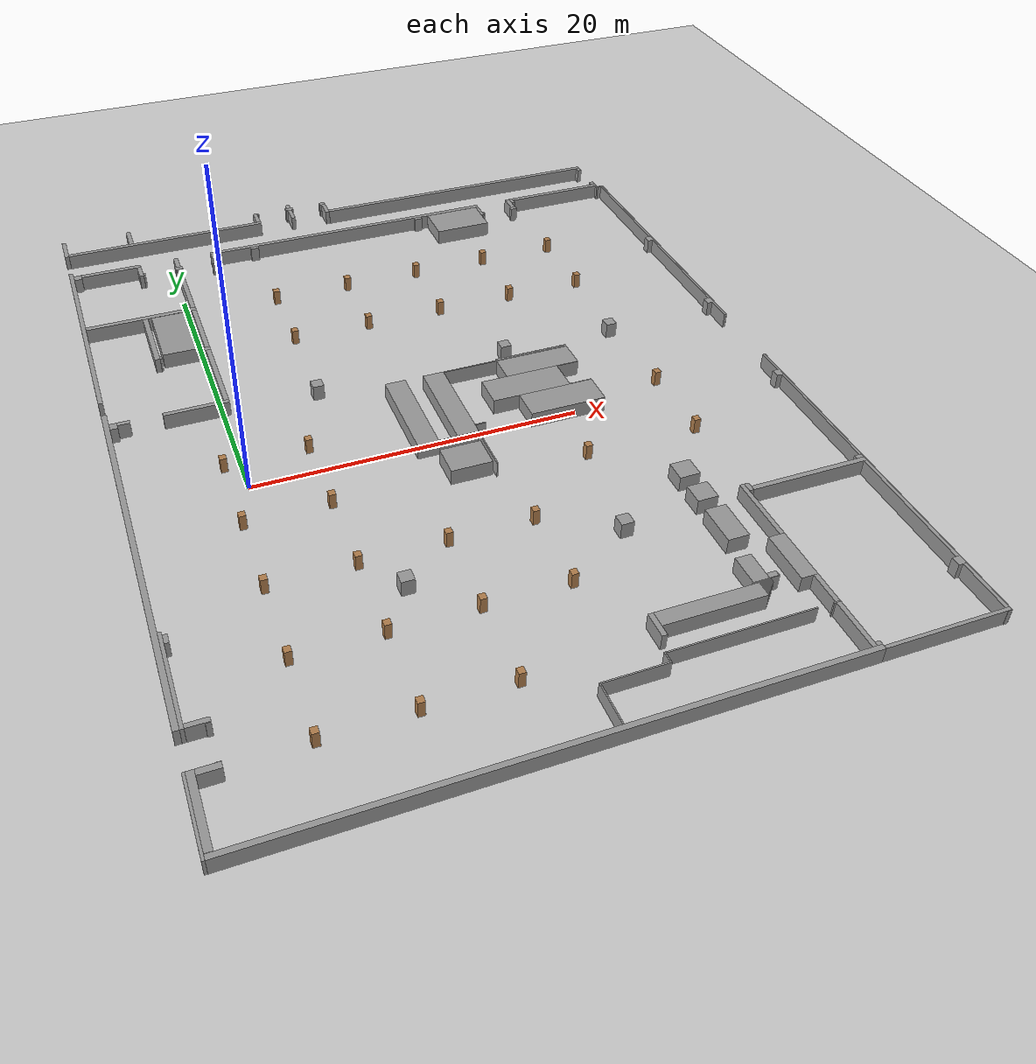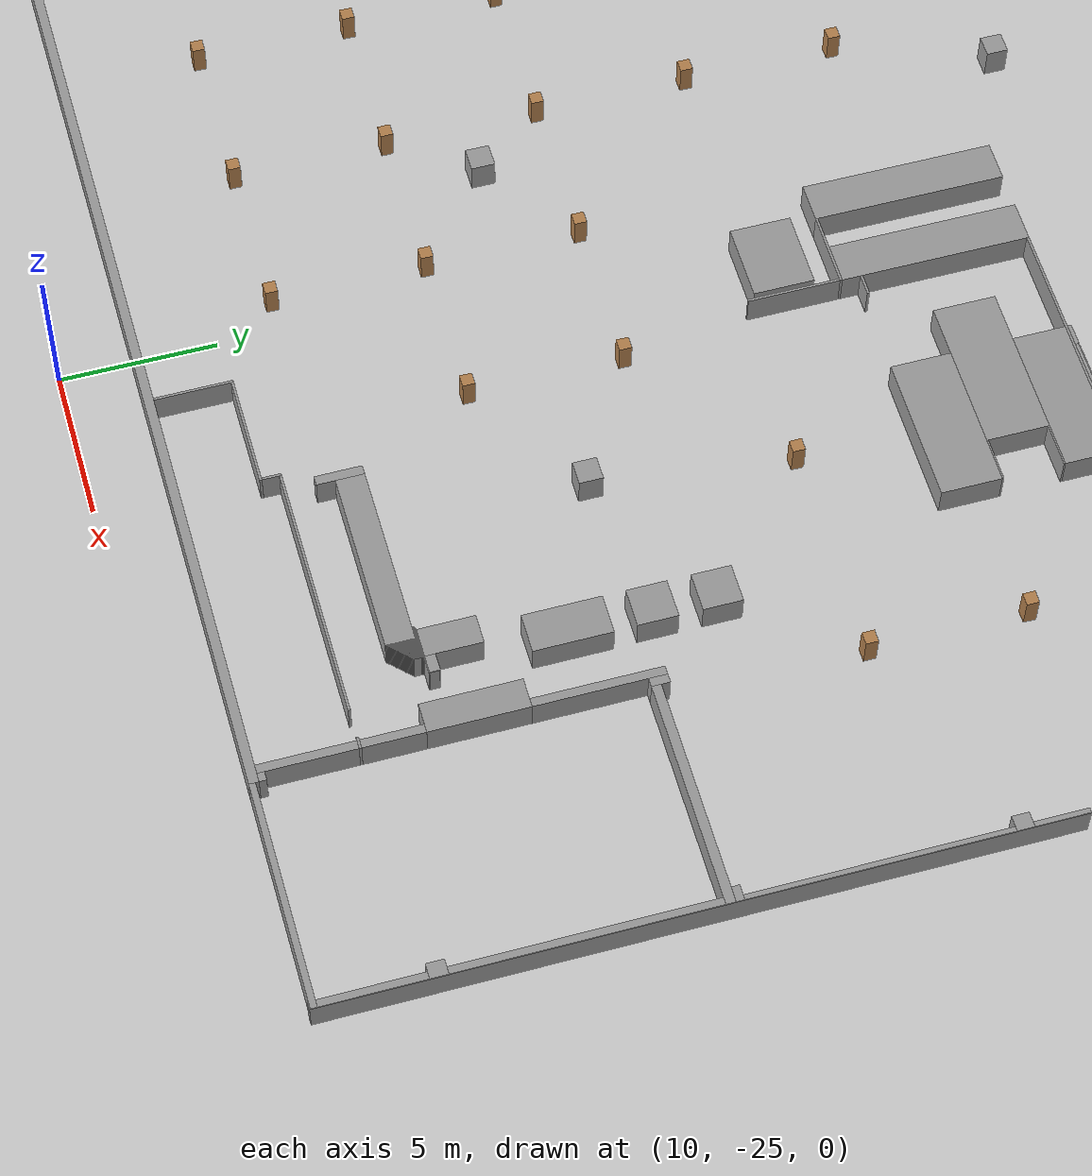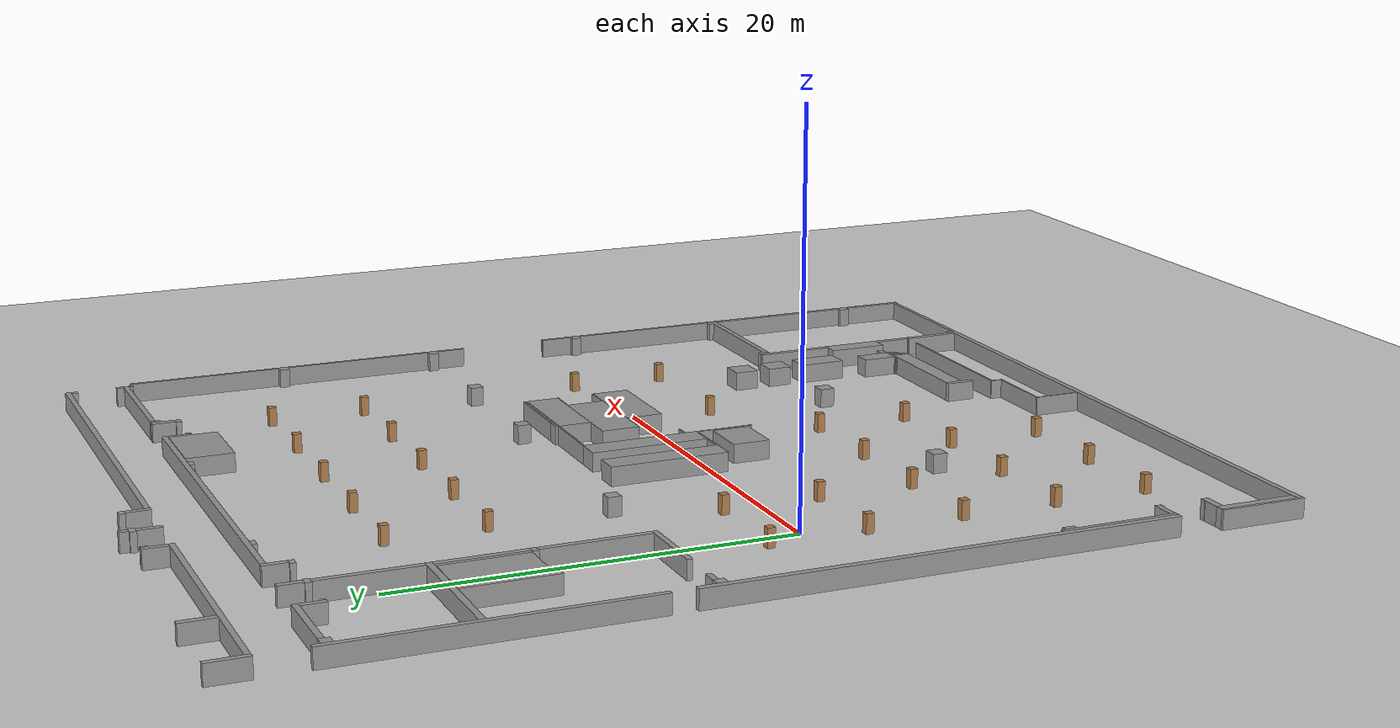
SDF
<sdf version="1.4">
 <world name="default">
  <physics type="ode">
   <gravity>0 0 -9.81</gravity>
   <ode>
    <solver><type>quick</type><iters>20</iters><sor>1</sor></solver>
    <constraints>
     <cfm>0</cfm>
     <erp>0.2</erp>
     <contact_max_correcting_vel>100</contact_max_correcting_vel>
     <contact_surface_layer>0</contact_surface_layer>
    </constraints>
   </ode>
   <real_time_update_rate>1000</real_time_update_rate>
   <max_step_size>0.001</max_step_size>
   <real_time_factor>1</real_time_factor>
   <max_contacts>20</max_contacts>
  </physics>
  <light name="sun" type="directional">
   <pose>0 0 10 0 -0 0</pose>
   <diffuse>0.8 0.8 0.8 1</diffuse>
   <specular>0.2 0.2 0.2 1</specular>
   <attenuation>
    <range>1000</range>
    <constant>0.9</constant>
    <linear>0.01</linear>
    <quadratic>0.001</quadratic>
   </attenuation>
   <direction>0.5 0.1 -0.9</direction>
  </light>
  <model name="ground_plane">
   <static>1</static>
   <link name="link">
    <collision name="collision">
     <geometry><plane><normal>0 0 1</normal><size>100 100</size></plane></geometry>
     <surface><friction><ode><mu>100</mu><mu2>50</mu2></ode></friction></surface>
    </collision>
    <visual name="visual">
     <cast_shadows>0</cast_shadows>
     <geometry><plane><normal>0 0 1</normal><size>100 100</size></plane></geometry>
     <material>
      <script><uri>file://media/materials/scripts/gazebo.material</uri><name>Gazebo/Grey</name></script>
     </material>
    </visual>
    <velocity_decay><linear>0</linear><angular>0</angular></velocity_decay>
   </link>
  </model>
  <model name="walls">
   <static>1</static>
   <link name="Wall_0">
    <collision name="Wall_0_Collision">
     <geometry><box><size>4.51915 0.15319 1</size></box></geometry>
     <pose>2.28511 -0.0766 0.5 0 -0 0</pose>
    </collision>
    <visual name="Wall_0_Visual">
     <geometry><box><size>4.51915 0.15319 1</size></box></geometry>
     <material>
      <script><uri>file://media/materials/scripts/gazebo.material</uri><name>Gazebo/Grey</name></script>
     </material>
     <pose>2.28511 -0.0766 0.5 0 -0 0</pose>
    </visual>
    <velocity_decay><linear>0</linear><angular>0</angular></velocity_decay>
   </link>
   <link name="Wall_1">
    <collision name="Wall_1_Collision">
     <geometry><box><size>24.0766 0.33191 1</size></box></geometry>
     <pose>18.8553 -0.16596 0.5 0 -0 0</pose>
    </collision>
    <visual name="Wall_1_Visual">
     <geometry><box><size>24.0766 0.33191 1</size></box></geometry>
     <material>
      <script><uri>file://media/materials/scripts/gazebo.material</uri><name>Gazebo/Grey</name></script>
     </material>
     <pose>18.8553 -0.16596 0.5 0 -0 0</pose>
    </visual>
    <velocity_decay><linear>0</linear><angular>0</angular></velocity_decay>
   </link>
   <link name="Wall_2">
    <collision name="Wall_2_Collision">
     <geometry><box><size>15.4979 0.28085 1</size></box></geometry>
     <pose>39.8426 -0.14043 0.5 0 -0 0</pose>
    </collision>
    <visual name="Wall_2_Visual">
     <geometry><box><size>15.4979 0.28085 1</size></box></geometry>
     <material>
      <script><uri>file://media/materials/scripts/gazebo.material</uri><name>Gazebo/Grey</name></script>
     </material>
     <pose>39.8426 -0.14043 0.5 0 -0 0</pose>
    </visual>
    <velocity_decay><linear>0</linear><angular>0</angular></velocity_decay>
   </link>
   <link name="Wall_3">
    <collision name="Wall_3_Collision">
     <geometry><box><size>2.01702 0.28085 1</size></box></geometry>
     <pose>51 -0.14043 0.5 0 -0 0</pose>
    </collision>
    <visual name="Wall_3_Visual">
     <geometry><box><size>2.01702 0.28085 1</size></box></geometry>
     <material>
      <script><uri>file://media/materials/scripts/gazebo.material</uri><name>Gazebo/Grey</name></script>
     </material>
     <pose>51 -0.14043 0.5 0 -0 0</pose>
    </visual>
    <velocity_decay><linear>0</linear><angular>0</angular></velocity_decay>
   </link>
   <link name="Wall_4">
    <collision name="Wall_4_Collision">
     <geometry><box><size>0.30638 32.7319 1</size></box></geometry>
     <pose>0.17872 -16.5191 0.5 0 -0 0</pose>
    </collision>
    <visual name="Wall_4_Visual">
     <geometry><box><size>0.30638 32.7319 1</size></box></geometry>
     <material>
      <script><uri>file://media/materials/scripts/gazebo.material</uri><name>Gazebo/Grey</name></script>
     </material>
     <pose>0.17872 -16.5191 0.5 0 -0 0</pose>
    </visual>
    <velocity_decay><linear>0</linear><angular>0</angular></velocity_decay>
   </link>
   <link name="Wall_5">
    <collision name="Wall_5_Collision">
     <geometry><box><size>4.18723 0.40851 1</size></box></geometry>
     <pose>2.45106 -0.35745 0.5 0 -0 0</pose>
    </collision>
    <visual name="Wall_5_Visual">
     <geometry><box><size>4.18723 0.40851 1</size></box></geometry>
     <material>
      <script><uri>file://media/materials/scripts/gazebo.material</uri><name>Gazebo/Grey</name></script>
     </material>
     <pose>2.45106 -0.35745 0.5 0 -0 0</pose>
    </visual>
    <velocity_decay><linear>0</linear><angular>0</angular></velocity_decay>
   </link>
   <link name="Wall_6">
    <collision name="Wall_6_Collision">
     <geometry><box><size>0.02553 0.30638 1</size></box></geometry>
     <pose>0.34468 -0.40851 0.5 0 -0 0</pose>
    </collision>
    <visual name="Wall_6_Visual">
     <geometry><box><size>0.02553 0.30638 1</size></box></geometry>
     <material>
      <script><uri>file://media/materials/scripts/gazebo.material</uri><name>Gazebo/Grey</name></script>
     </material>
     <pose>0.34468 -0.40851 0.5 0 -0 0</pose>
    </visual>
    <velocity_decay><linear>0</linear><angular>0</angular></velocity_decay>
   </link>
   <link name="Wall_7">
    <collision name="Wall_7_Collision">
     <geometry><box><size>0.33191 7.17447 1</size></box></geometry>
     <pose>40.4043 -3.86809 0.5 0 -0 0</pose>
    </collision>
    <visual name="Wall_7_Visual">
     <geometry><box><size>0.33191 7.17447 1</size></box></geometry>
     <material>
      <script><uri>file://media/materials/scripts/gazebo.material</uri><name>Gazebo/Grey</name></script>
     </material>
     <pose>40.4043 -3.86809 0.5 0 -0 0</pose>
    </visual>
    <velocity_decay><linear>0</linear><angular>0</angular></velocity_decay>
   </link>
   <link name="Wall_8">
    <collision name="Wall_8_Collision">
     <geometry><box><size>0.53617 0.51064 1</size></box></geometry>
     <pose>46.9149 -0.53617 0.5 0 -0 0</pose>
    </collision>
    <visual name="Wall_8_Visual">
     <geometry><box><size>0.53617 0.51064 1</size></box></geometry>
     <material>
      <script><uri>file://media/materials/scripts/gazebo.material</uri><name>Gazebo/Grey</name></script>
     </material>
     <pose>46.9149 -0.53617 0.5 0 -0 0</pose>
    </visual>
    <velocity_decay><linear>0</linear><angular>0</angular></velocity_decay>
   </link>
   <link name="Wall_9">
    <collision name="Wall_9_Collision">
     <geometry><box><size>0.28085 13.8383 1</size></box></geometry>
     <pose>50.1319 -7.2 0.5 0 -0 0</pose>
    </collision>
    <visual name="Wall_9_Visual">
     <geometry><box><size>0.28085 13.8383 1</size></box></geometry>
     <material>
      <script><uri>file://media/materials/scripts/gazebo.material</uri><name>Gazebo/Grey</name></script>
     </material>
     <pose>50.1319 -7.2 0.5 0 -0 0</pose>
    </visual>
    <velocity_decay><linear>0</linear><angular>0</angular></velocity_decay>
   </link>
   <link name="Wall_10">
    <collision name="Wall_10_Collision">
     <geometry><box><size>6.0766 0.20426 1</size></box></geometry>
     <pose>9.85532 -0.43404 0.5 0 -0 0</pose>
    </collision>
    <visual name="Wall_10_Visual">
     <geometry><box><size>6.0766 0.20426 1</size></box></geometry>
     <material>
      <script><uri>file://media/materials/scripts/gazebo.material</uri><name>Gazebo/Grey</name></script>
     </material>
     <pose>9.85532 -0.43404 0.5 0 -0 0</pose>
    </visual>
    <velocity_decay><linear>0</linear><angular>0</angular></velocity_decay>
   </link>
   <link name="Wall_11">
    <collision name="Wall_11_Collision">
     <geometry><box><size>0.53617 0.45957 1</size></box></geometry>
     <pose>29.6553 -0.5617 0.5 0 -0 0</pose>
    </collision>
    <visual name="Wall_11_Visual">
     <geometry><box><size>0.53617 0.45957 1</size></box></geometry>
     <material>
      <script><uri>file://media/materials/scripts/gazebo.material</uri><name>Gazebo/Grey</name></script>
     </material>
     <pose>29.6553 -0.5617 0.5 0 -0 0</pose>
    </visual>
    <velocity_decay><linear>0</linear><angular>0</angular></velocity_decay>
   </link>
   <link name="Wall_12">
    <collision name="Wall_12_Collision">
     <geometry><box><size>0.28085 1.22553 1</size></box></geometry>
     <pose>6.95745 -1.14894 0.5 0 -0 0</pose>
    </collision>
    <visual name="Wall_12_Visual">
     <geometry><box><size>0.28085 1.22553 1</size></box></geometry>
     <material>
      <script><uri>file://media/materials/scripts/gazebo.material</uri><name>Gazebo/Grey</name></script>
     </material>
     <pose>6.95745 -1.14894 0.5 0 -0 0</pose>
    </visual>
    <velocity_decay><linear>0</linear><angular>0</angular></velocity_decay>
   </link>
   <link name="Wall_13">
    <collision name="Wall_13_Collision">
     <geometry><box><size>0.58723 0.25532 1</size></box></geometry>
     <pose>12.3702 -0.66383 0.5 0 -0 0</pose>
    </collision>
    <visual name="Wall_13_Visual">
     <geometry><box><size>0.58723 0.25532 1</size></box></geometry>
     <material>
      <script><uri>file://media/materials/scripts/gazebo.material</uri><name>Gazebo/Grey</name></script>
     </material>
     <pose>12.3702 -0.66383 0.5 0 -0 0</pose>
    </visual>
    <velocity_decay><linear>0</linear><angular>0</angular></velocity_decay>
   </link>
   <link name="Wall_14">
    <collision name="Wall_14_Collision">
     <geometry><box><size>0.35745 1.2 1</size></box></geometry>
     <pose>4.36596 -1.1617 0.5 0 -0 0</pose>
    </collision>
    <visual name="Wall_14_Visual">
     <geometry><box><size>0.35745 1.2 1</size></box></geometry>
     <material>
      <script><uri>file://media/materials/scripts/gazebo.material</uri><name>Gazebo/Grey</name></script>
     </material>
     <pose>4.36596 -1.1617 0.5 0 -0 0</pose>
    </visual>
    <velocity_decay><linear>0</linear><angular>0</angular></velocity_decay>
   </link>
   <link name="Wall_15">
    <collision name="Wall_15_Collision">
     <geometry><box><size>0.28085 0.74043 1</size></box></geometry>
     <pose>29.783 -1.1617 0.5 0 -0 0</pose>
    </collision>
    <visual name="Wall_15_Visual">
     <geometry><box><size>0.28085 0.74043 1</size></box></geometry>
     <material>
      <script><uri>file://media/materials/scripts/gazebo.material</uri><name>Gazebo/Grey</name></script>
     </material>
     <pose>29.783 -1.1617 0.5 0 -0 0</pose>
    </visual>
    <velocity_decay><linear>0</linear><angular>0</angular></velocity_decay>
   </link>
   <link name="Wall_16">
    <collision name="Wall_16_Collision">
     <geometry><box><size>0.30638 4.05957 1</size></box></geometry>
     <pose>47.0298 -2.82128 0.5 0 -0 0</pose>
    </collision>
    <visual name="Wall_16_Visual">
     <geometry><box><size>0.30638 4.05957 1</size></box></geometry>
     <material>
      <script><uri>file://media/materials/scripts/gazebo.material</uri><name>Gazebo/Grey</name></script>
     </material>
     <pose>47.0298 -2.82128 0.5 0 -0 0</pose>
    </visual>
    <velocity_decay><linear>0</linear><angular>0</angular></velocity_decay>
   </link>
   <link name="Wall_17">
    <collision name="Wall_17_Collision">
     <geometry><box><size>0.02553 0.30638 1</size></box></geometry>
     <pose>4.55745 -1.60851 0.5 0 -0 0</pose>
    </collision>
    <visual name="Wall_17_Visual">
     <geometry><box><size>0.02553 0.30638 1</size></box></geometry>
     <material>
      <script><uri>file://media/materials/scripts/gazebo.material</uri><name>Gazebo/Grey</name></script>
     </material>
     <pose>4.55745 -1.60851 0.5 0 -0 0</pose>
    </visual>
    <velocity_decay><linear>0</linear><angular>0</angular></velocity_decay>
   </link>
   <link name="Wall_18">
    <collision name="Wall_18_Collision">
     <geometry><box><size>0.05106 0.28085 1</size></box></geometry>
     <pose>6.79149 -1.62128 0.5 0 -0 0</pose>
    </collision>
    <visual name="Wall_18_Visual">
     <geometry><box><size>0.05106 0.28085 1</size></box></geometry>
     <material>
      <script><uri>file://media/materials/scripts/gazebo.material</uri><name>Gazebo/Grey</name></script>
     </material>
     <pose>6.79149 -1.62128 0.5 0 -0 0</pose>
    </visual>
    <velocity_decay><linear>0</linear><angular>0</angular></velocity_decay>
   </link>
   <link name="Wall_19">
    <collision name="Wall_19_Collision">
     <geometry><box><size>0.28085 3.98298 1</size></box></geometry>
     <pose>29.783 -5.46383 0.5 0 -0 0</pose>
    </collision>
    <visual name="Wall_19_Visual">
     <geometry><box><size>0.28085 3.98298 1</size></box></geometry>
     <material>
      <script><uri>file://media/materials/scripts/gazebo.material</uri><name>Gazebo/Grey</name></script>
     </material>
     <pose>29.783 -5.46383 0.5 0 -0 0</pose>
    </visual>
    <velocity_decay><linear>0</linear><angular>0</angular></velocity_decay>
   </link>
   <link name="Wall_20">
    <collision name="Wall_20_Collision">
     <geometry><box><size>4.77447 0.33191 1</size></box></geometry>
     <pose>37.8511 -4.09787 0.5 0 -0 0</pose>
    </collision>
    <visual name="Wall_20_Visual">
     <geometry><box><size>4.77447 0.33191 1</size></box></geometry>
     <material>
      <script><uri>file://media/materials/scripts/gazebo.material</uri><name>Gazebo/Grey</name></script>
     </material>
     <pose>37.8511 -4.09787 0.5 0 -0 0</pose>
    </visual>
    <velocity_decay><linear>0</linear><angular>0</angular></velocity_decay>
   </link>
   <link name="Wall_21">
    <collision name="Wall_21_Collision">
     <geometry><box><size>0.28085 0.10213 1</size></box></geometry>
     <pose>35.6043 -4.31489 0.5 0 -0 0</pose>
    </collision>
    <visual name="Wall_21_Visual">
     <geometry><box><size>0.28085 0.10213 1</size></box></geometry>
     <material>
      <script><uri>file://media/materials/scripts/gazebo.material</uri><name>Gazebo/Grey</name></script>
     </material>
     <pose>35.6043 -4.31489 0.5 0 -0 0</pose>
    </visual>
    <velocity_decay><linear>0</linear><angular>0</angular></velocity_decay>
   </link>
   <link name="Wall_22">
    <collision name="Wall_22_Collision">
     <geometry><box><size>4.41702 2.42553 1</size></box></geometry>
     <pose>38.0043 -5.70638 0.5 0 -0 0</pose>
    </collision>
    <visual name="Wall_22_Visual">
     <geometry><box><size>4.41702 2.42553 1</size></box></geometry>
     <material>
      <script><uri>file://media/materials/scripts/gazebo.material</uri><name>Gazebo/Grey</name></script>
     </material>
     <pose>38.0043 -5.70638 0.5 0 -0 0</pose>
    </visual>
    <velocity_decay><linear>0</linear><angular>0</angular></velocity_decay>
   </link>
   <link name="Wall_23">
    <collision name="Wall_23_Collision">
     <geometry><box><size>1.73617 0.30638 1</size></box></geometry>
     <pose>51.1404 -4.69787 0.5 0 -0 0</pose>
    </collision>
    <visual name="Wall_23_Visual">
     <geometry><box><size>1.73617 0.30638 1</size></box></geometry>
     <material>
      <script><uri>file://media/materials/scripts/gazebo.material</uri><name>Gazebo/Grey</name></script>
     </material>
     <pose>51.1404 -4.69787 0.5 0 -0 0</pose>
    </visual>
    <velocity_decay><linear>0</linear><angular>0</angular></velocity_decay>
   </link>
   <link name="Wall_24">
    <collision name="Wall_24_Collision">
     <geometry><box><size>1.2 0.28085 1</size></box></geometry>
     <pose>46.2766 -4.71064 0.5 0 -0 0</pose>
    </collision>
    <visual name="Wall_24_Visual">
     <geometry><box><size>1.2 0.28085 1</size></box></geometry>
     <material>
      <script><uri>file://media/materials/scripts/gazebo.material</uri><name>Gazebo/Grey</name></script>
     </material>
     <pose>46.2766 -4.71064 0.5 0 -0 0</pose>
    </visual>
    <velocity_decay><linear>0</linear><angular>0</angular></velocity_decay>
   </link>
   <link name="Wall_25">
    <collision name="Wall_25_Collision">
     <geometry><box><size>0.28085 0.12766 1</size></box></geometry>
     <pose>45.817 -4.91489 0.5 0 -0 0</pose>
    </collision>
    <visual name="Wall_25_Visual">
     <geometry><box><size>0.28085 0.12766 1</size></box></geometry>
     <material>
      <script><uri>file://media/materials/scripts/gazebo.material</uri><name>Gazebo/Grey</name></script>
     </material>
     <pose>45.817 -4.91489 0.5 0 -0 0</pose>
    </visual>
    <velocity_decay><linear>0</linear><angular>0</angular></velocity_decay>
   </link>
   <link name="Wall_26">
    <collision name="Wall_26_Collision">
     <geometry><box><size>0.30638 0.40851 1</size></box></geometry>
     <pose>35.5915 -7.25106 0.5 0 -0 0</pose>
    </collision>
    <visual name="Wall_26_Visual">
     <geometry><box><size>0.30638 0.40851 1</size></box></geometry>
     <material>
      <script><uri>file://media/materials/scripts/gazebo.material</uri><name>Gazebo/Grey</name></script>
     </material>
     <pose>35.5915 -7.25106 0.5 0 -0 0</pose>
    </visual>
    <velocity_decay><linear>0</linear><angular>0</angular></velocity_decay>
   </link>
   <link name="Wall_27">
    <collision name="Wall_27_Collision">
     <geometry><box><size>0.30638 0.51064 1</size></box></geometry>
     <pose>45.8298 -7.30213 0.5 0 -0 0</pose>
    </collision>
    <visual name="Wall_27_Visual">
     <geometry><box><size>0.30638 0.51064 1</size></box></geometry>
     <material>
      <script><uri>file://media/materials/scripts/gazebo.material</uri><name>Gazebo/Grey</name></script>
     </material>
     <pose>45.8298 -7.30213 0.5 0 -0 0</pose>
    </visual>
    <velocity_decay><linear>0</linear><angular>0</angular></velocity_decay>
   </link>
   <link name="Wall_28">
    <collision name="Wall_28_Collision">
     <geometry><box><size>5.51489 0.30638 1</size></box></geometry>
     <pose>32.6808 -7.30213 0.5 0 -0 0</pose>
    </collision>
    <visual name="Wall_28_Visual">
     <geometry><box><size>5.51489 0.30638 1</size></box></geometry>
     <material>
      <script><uri>file://media/materials/scripts/gazebo.material</uri><name>Gazebo/Grey</name></script>
     </material>
     <pose>32.6808 -7.30213 0.5 0 -0 0</pose>
    </visual>
    <velocity_decay><linear>0</linear><angular>0</angular></velocity_decay>
   </link>
   <link name="Wall_29">
    <collision name="Wall_29_Collision">
     <geometry><box><size>4.49362 0.30638 1</size></box></geometry>
     <pose>37.9915 -7.30213 0.5 0 -0 0</pose>
    </collision>
    <visual name="Wall_29_Visual">
     <geometry><box><size>4.49362 0.30638 1</size></box></geometry>
     <material>
      <script><uri>file://media/materials/scripts/gazebo.material</uri><name>Gazebo/Grey</name></script>
     </material>
     <pose>37.9915 -7.30213 0.5 0 -0 0</pose>
    </visual>
    <velocity_decay><linear>0</linear><angular>0</angular></velocity_decay>
   </link>
   <link name="Wall_30">
    <collision name="Wall_30_Collision">
     <geometry><box><size>5.10638 0.30638 1</size></box></geometry>
     <pose>43.1234 -7.30213 0.5 0 -0 0</pose>
    </collision>
    <visual name="Wall_30_Visual">
     <geometry><box><size>5.10638 0.30638 1</size></box></geometry>
     <material>
      <script><uri>file://media/materials/scripts/gazebo.material</uri><name>Gazebo/Grey</name></script>
     </material>
     <pose>43.1234 -7.30213 0.5 0 -0 0</pose>
    </visual>
    <velocity_decay><linear>0</linear><angular>0</angular></velocity_decay>
   </link>
   <link name="Wall_31">
    <collision name="Wall_31_Collision">
     <geometry><box><size>1.2 0.30638 1</size></box></geometry>
     <pose>46.583 -7.30213 0.5 0 -0 0</pose>
    </collision>
    <visual name="Wall_31_Visual">
     <geometry><box><size>1.2 0.30638 1</size></box></geometry>
     <material>
      <script><uri>file://media/materials/scripts/gazebo.material</uri><name>Gazebo/Grey</name></script>
     </material>
     <pose>46.583 -7.30213 0.5 0 -0 0</pose>
    </visual>
    <velocity_decay><linear>0</linear><angular>0</angular></velocity_decay>
   </link>
   <link name="Wall_32">
    <collision name="Wall_32_Collision">
     <geometry><box><size>0.28085 0.43404 1</size></box></geometry>
     <pose>45.817 -9.84255 0.5 0 -0 0</pose>
    </collision>
    <visual name="Wall_32_Visual">
     <geometry><box><size>0.28085 0.43404 1</size></box></geometry>
     <material>
      <script><uri>file://media/materials/scripts/gazebo.material</uri><name>Gazebo/Grey</name></script>
     </material>
     <pose>45.817 -9.84255 0.5 0 -0 0</pose>
    </visual>
    <velocity_decay><linear>0</linear><angular>0</angular></velocity_decay>
   </link>
   <link name="Wall_33">
    <collision name="Wall_33_Collision">
     <geometry><box><size>1.22553 0.30638 1</size></box></geometry>
     <pose>46.5702 -9.90638 0.5 0 -0 0</pose>
    </collision>
    <visual name="Wall_33_Visual">
     <geometry><box><size>1.22553 0.30638 1</size></box></geometry>
     <material>
      <script><uri>file://media/materials/scripts/gazebo.material</uri><name>Gazebo/Grey</name></script>
     </material>
     <pose>46.5702 -9.90638 0.5 0 -0 0</pose>
    </visual>
    <velocity_decay><linear>0</linear><angular>0</angular></velocity_decay>
   </link>
   <link name="Wall_34">
    <collision name="Wall_34_Collision">
     <geometry><box><size>0.28085 19.9404 1</size></box></geometry>
     <pose>47.0425 -20.0298 0.5 0 -0 0</pose>
    </collision>
    <visual name="Wall_34_Visual">
     <geometry><box><size>0.28085 19.9404 1</size></box></geometry>
     <material>
      <script><uri>file://media/materials/scripts/gazebo.material</uri><name>Gazebo/Grey</name></script>
     </material>
     <pose>47.0425 -20.0298 0.5 0 -0 0</pose>
    </visual>
    <velocity_decay><linear>0</linear><angular>0</angular></velocity_decay>
   </link>
   <link name="Wall_35">
    <collision name="Wall_35_Collision">
     <geometry><box><size>0.76596 0.76596 1</size></box></geometry>
     <pose>12.383 -12.8425 0.5 0 -0 0</pose>
    </collision>
    <visual name="Wall_35_Visual">
     <geometry><box><size>0.76596 0.76596 1</size></box></geometry>
     <material>
      <script><uri>file://media/materials/scripts/gazebo.material</uri><name>Gazebo/Grey</name></script>
     </material>
     <pose>12.383 -12.8425 0.5 0 -0 0</pose>
    </visual>
    <velocity_decay><linear>0</linear><angular>0</angular></velocity_decay>
   </link>
   <link name="Wall_36">
    <collision name="Wall_36_Collision">
     <geometry><box><size>0.68936 0.68936 1</size></box></geometry>
     <pose>29.6553 -12.8553 0.5 0 -0 0</pose>
    </collision>
    <visual name="Wall_36_Visual">
     <geometry><box><size>0.68936 0.68936 1</size></box></geometry>
     <material>
      <script><uri>file://media/materials/scripts/gazebo.material</uri><name>Gazebo/Grey</name></script>
     </material>
     <pose>29.6553 -12.8553 0.5 0 -0 0</pose>
    </visual>
    <velocity_decay><linear>0</linear><angular>0</angular></velocity_decay>
   </link>
   <link name="Wall_37">
    <collision name="Wall_37_Collision">
     <geometry><box><size>0.25532 0.5617 1</size></box></geometry>
     <pose>46.7745 -12.8681 0.5 0 -0 0</pose>
    </collision>
    <visual name="Wall_37_Visual">
     <geometry><box><size>0.25532 0.5617 1</size></box></geometry>
     <material>
      <script><uri>file://media/materials/scripts/gazebo.material</uri><name>Gazebo/Grey</name></script>
     </material>
     <pose>46.7745 -12.8681 0.5 0 -0 0</pose>
    </visual>
    <velocity_decay><linear>0</linear><angular>0</angular></velocity_decay>
   </link>
   <link name="Wall_38">
    <collision name="Wall_38_Collision">
     <geometry><box><size>1.25106 0.28085 1</size></box></geometry>
     <pose>50.8979 -13.9787 0.5 0 -0 0</pose>
    </collision>
    <visual name="Wall_38_Visual">
     <geometry><box><size>1.25106 0.28085 1</size></box></geometry>
     <material>
      <script><uri>file://media/materials/scripts/gazebo.material</uri><name>Gazebo/Grey</name></script>
     </material>
     <pose>50.8979 -13.9787 0.5 0 -0 0</pose>
    </visual>
    <velocity_decay><linear>0</linear><angular>0</angular></velocity_decay>
   </link>
   <link name="Wall_39">
    <collision name="Wall_39_Collision">
     <geometry><box><size>0.33191 0.12766 1</size></box></geometry>
     <pose>51.3575 -14.183 0.5 0 -0 0</pose>
    </collision>
    <visual name="Wall_39_Visual">
     <geometry><box><size>0.33191 0.12766 1</size></box></geometry>
     <material>
      <script><uri>file://media/materials/scripts/gazebo.material</uri><name>Gazebo/Grey</name></script>
     </material>
     <pose>51.3575 -14.183 0.5 0 -0 0</pose>
    </visual>
    <velocity_decay><linear>0</linear><angular>0</angular></velocity_decay>
   </link>
   <link name="Wall_40">
    <collision name="Wall_40_Collision">
     <geometry><box><size>0.33191 0.53617 1</size></box></geometry>
     <pose>51.383 -16.5574 0.5 0 -0 0</pose>
    </collision>
    <visual name="Wall_40_Visual">
     <geometry><box><size>0.33191 0.53617 1</size></box></geometry>
     <material>
      <script><uri>file://media/materials/scripts/gazebo.material</uri><name>Gazebo/Grey</name></script>
     </material>
     <pose>51.383 -16.5574 0.5 0 -0 0</pose>
    </visual>
    <velocity_decay><linear>0</linear><angular>0</angular></velocity_decay>
   </link>
   <link name="Wall_41">
    <collision name="Wall_41_Collision">
     <geometry><box><size>1.22553 0.28085 1</size></box></geometry>
     <pose>50.6043 -16.5574 0.5 0 -0 0</pose>
    </collision>
    <visual name="Wall_41_Visual">
     <geometry><box><size>1.22553 0.28085 1</size></box></geometry>
     <material>
      <script><uri>file://media/materials/scripts/gazebo.material</uri><name>Gazebo/Grey</name></script>
     </material>
     <pose>50.6043 -16.5574 0.5 0 -0 0</pose>
    </visual>
    <velocity_decay><linear>0</linear><angular>0</angular></velocity_decay>
   </link>
   <link name="Wall_42">
    <collision name="Wall_42_Collision">
     <geometry><box><size>0.45957 0.30638 1</size></box></geometry>
     <pose>51.7787 -16.5702 0.5 0 -0 0</pose>
    </collision>
    <visual name="Wall_42_Visual">
     <geometry><box><size>0.45957 0.30638 1</size></box></geometry>
     <material>
      <script><uri>file://media/materials/scripts/gazebo.material</uri><name>Gazebo/Grey</name></script>
     </material>
     <pose>51.7787 -16.5702 0.5 0 -0 0</pose>
    </visual>
    <velocity_decay><linear>0</linear><angular>0</angular></velocity_decay>
   </link>
   <link name="Wall_43">
    <collision name="Wall_43_Collision">
     <geometry><box><size>6.22979 1.30213 1</size></box></geometry>
     <pose>25.0213 -17.3745 0.5 0 -0 0</pose>
    </collision>
    <visual name="Wall_43_Visual">
     <geometry><box><size>6.22979 1.30213 1</size></box></geometry>
     <material>
      <script><uri>file://media/materials/scripts/gazebo.material</uri><name>Gazebo/Grey</name></script>
     </material>
     <pose>25.0213 -17.3745 0.5 0 -0 0</pose>
    </visual>
    <velocity_decay><linear>0</linear><angular>0</angular></velocity_decay>
   </link>
   <link name="Wall_44">
    <collision name="Wall_44_Collision">
     <geometry><box><size>1.96596 2.50213 1</size></box></geometry>
     <pose>20.1575 -19.0213 0.5 0 -0 0</pose>
    </collision>
    <visual name="Wall_44_Visual">
     <geometry><box><size>1.96596 2.50213 1</size></box></geometry>
     <material>
      <script><uri>file://media/materials/scripts/gazebo.material</uri><name>Gazebo/Grey</name></script>
     </material>
     <pose>20.1575 -19.0213 0.5 0 -0 0</pose>
    </visual>
    <velocity_decay><linear>0</linear><angular>0</angular></velocity_decay>
   </link>
   <link name="Wall_45">
    <collision name="Wall_45_Collision">
     <geometry><box><size>0.0766 2.4766 1</size></box></geometry>
     <pose>21.9447 -19.2638 0.5 0 -0 0</pose>
    </collision>
    <visual name="Wall_45_Visual">
     <geometry><box><size>0.0766 2.4766 1</size></box></geometry>
     <material>
      <script><uri>file://media/materials/scripts/gazebo.material</uri><name>Gazebo/Grey</name></script>
     </material>
     <pose>21.9447 -19.2638 0.5 0 -0 0</pose>
    </visual>
    <velocity_decay><linear>0</linear><angular>0</angular></velocity_decay>
   </link>
   <link name="Wall_46">
    <collision name="Wall_46_Collision">
     <geometry><box><size>0.30638 0.40851 1</size></box></geometry>
     <pose>51.3702 -19.0979 0.5 0 -0 0</pose>
    </collision>
    <visual name="Wall_46_Visual">
     <geometry><box><size>0.30638 0.40851 1</size></box></geometry>
     <material>
      <script><uri>file://media/materials/scripts/gazebo.material</uri><name>Gazebo/Grey</name></script>
     </material>
     <pose>51.3702 -19.0979 0.5 0 -0 0</pose>
    </visual>
    <velocity_decay><linear>0</linear><angular>0</angular></velocity_decay>
   </link>
   <link name="Wall_47">
    <collision name="Wall_47_Collision">
     <geometry><box><size>1.22553 0.28085 1</size></box></geometry>
     <pose>50.6043 -19.1617 0.5 0 -0 0</pose>
    </collision>
    <visual name="Wall_47_Visual">
     <geometry><box><size>1.22553 0.28085 1</size></box></geometry>
     <material>
      <script><uri>file://media/materials/scripts/gazebo.material</uri><name>Gazebo/Grey</name></script>
     </material>
     <pose>50.6043 -19.1617 0.5 0 -0 0</pose>
    </visual>
    <velocity_decay><linear>0</linear><angular>0</angular></velocity_decay>
   </link>
   <link name="Wall_48">
    <collision name="Wall_48_Collision">
     <geometry><box><size>2.50213 0.0766 1</size></box></geometry>
     <pose>1.58298 -19.1362 0.5 0 -0 0</pose>
    </collision>
    <visual name="Wall_48_Visual">
     <geometry><box><size>2.50213 0.0766 1</size></box></geometry>
     <material>
      <script><uri>file://media/materials/scripts/gazebo.material</uri><name>Gazebo/Grey</name></script>
     </material>
     <pose>1.58298 -19.1362 0.5 0 -0 0</pose>
    </visual>
    <velocity_decay><linear>0</linear><angular>0</angular></velocity_decay>
   </link>
   <link name="Wall_49">
    <collision name="Wall_49_Collision">
     <geometry><box><size>0.0766 3.70213 1</size></box></geometry>
     <pose>2.79574 -21.0255 0.5 0 -0 0</pose>
    </collision>
    <visual name="Wall_49_Visual">
     <geometry><box><size>0.0766 3.70213 1</size></box></geometry>
     <material>
      <script><uri>file://media/materials/scripts/gazebo.material</uri><name>Gazebo/Grey</name></script>
     </material>
     <pose>2.79574 -21.0255 0.5 0 -0 0</pose>
    </visual>
    <velocity_decay><linear>0</linear><angular>0</angular></velocity_decay>
   </link>
   <link name="Wall_50">
    <collision name="Wall_50_Collision">
     <geometry><box><size>6.15319 1.32766 1</size></box></geometry>
     <pose>25.0596 -19.8383 0.5 0 -0 0</pose>
    </collision>
    <visual name="Wall_50_Visual">
     <geometry><box><size>6.15319 1.32766 1</size></box></geometry>
     <material>
      <script><uri>file://media/materials/scripts/gazebo.material</uri><name>Gazebo/Grey</name></script>
     </material>
     <pose>25.0596 -19.8383 0.5 0 -0 0</pose>
    </visual>
    <velocity_decay><linear>0</linear><angular>0</angular></velocity_decay>
   </link>
   <link name="Wall_51">
    <collision name="Wall_51_Collision">
     <geometry><box><size>0.28085 20.4766 1</size></box></geometry>
     <pose>50.1319 -29.5404 0.5 0 -0 0</pose>
    </collision>
    <visual name="Wall_51_Visual">
     <geometry><box><size>0.28085 20.4766 1</size></box></geometry>
     <material>
      <script><uri>file://media/materials/scripts/gazebo.material</uri><name>Gazebo/Grey</name></script>
     </material>
     <pose>50.1319 -29.5404 0.5 0 -0 0</pose>
    </visual>
    <velocity_decay><linear>0</linear><angular>0</angular></velocity_decay>
   </link>
   <link name="Wall_52">
    <collision name="Wall_52_Collision">
     <geometry><box><size>2.98723 0.0766 1</size></box></geometry>
     <pose>20.4128 -20.4638 0.5 0 -0 0</pose>
    </collision>
    <visual name="Wall_52_Visual">
     <geometry><box><size>2.98723 0.0766 1</size></box></geometry>
     <material>
      <script><uri>file://media/materials/scripts/gazebo.material</uri><name>Gazebo/Grey</name></script>
     </material>
     <pose>20.4128 -20.4638 0.5 0 -0 0</pose>
    </visual>
    <velocity_decay><linear>0</linear><angular>0</angular></velocity_decay>
   </link>
   <link name="Wall_53">
    <collision name="Wall_53_Collision">
     <geometry><box><size>0.0766 0.68936 1</size></box></geometry>
     <pose>22.6085 -20.8468 0.5 0 -0 0</pose>
    </collision>
    <visual name="Wall_53_Visual">
     <geometry><box><size>0.0766 0.68936 1</size></box></geometry>
     <material>
      <script><uri>file://media/materials/scripts/gazebo.material</uri><name>Gazebo/Grey</name></script>
     </material>
     <pose>22.6085 -20.8468 0.5 0 -0 0</pose>
    </visual>
    <velocity_decay><linear>0</linear><angular>0</angular></velocity_decay>
   </link>
   <link name="Wall_54">
    <collision name="Wall_54_Collision">
     <geometry><box><size>0.0766 8.29787 1</size></box></geometry>
     <pose>28.0979 -24.6511 0.5 0 -0 0</pose>
    </collision>
    <visual name="Wall_54_Visual">
     <geometry><box><size>0.0766 8.29787 1</size></box></geometry>
     <material>
      <script><uri>file://media/materials/scripts/gazebo.material</uri><name>Gazebo/Grey</name></script>
     </material>
     <pose>28.0979 -24.6511 0.5 0 -0 0</pose>
    </visual>
    <velocity_decay><linear>0</linear><angular>0</angular></velocity_decay>
   </link>
   <link name="Wall_55">
    <collision name="Wall_55_Collision">
     <geometry><box><size>2.01702 5.00426 1</size></box></geometry>
     <pose>25.3404 -24.8681 0.5 0 -0 0</pose>
    </collision>
    <visual name="Wall_55_Visual">
     <geometry><box><size>2.01702 5.00426 1</size></box></geometry>
     <material>
      <script><uri>file://media/materials/scripts/gazebo.material</uri><name>Gazebo/Grey</name></script>
     </material>
     <pose>25.3404 -24.8681 0.5 0 -0 0</pose>
    </visual>
    <velocity_decay><linear>0</linear><angular>0</angular></velocity_decay>
   </link>
   <link name="Wall_56">
    <collision name="Wall_56_Collision">
     <geometry><box><size>0.61277 0.0766 1</size></box></geometry>
     <pose>3.14043 -22.8383 0.5 0 -0 0</pose>
    </collision>
    <visual name="Wall_56_Visual">
     <geometry><box><size>0.61277 0.0766 1</size></box></geometry>
     <material>
      <script><uri>file://media/materials/scripts/gazebo.material</uri><name>Gazebo/Grey</name></script>
     </material>
     <pose>3.14043 -22.8383 0.5 0 -0 0</pose>
    </visual>
    <velocity_decay><linear>0</linear><angular>0</angular></velocity_decay>
   </link>
   <link name="Wall_57">
    <collision name="Wall_57_Collision">
     <geometry><box><size>0.0766 8.42553 1</size></box></geometry>
     <pose>3.40851 -27.0894 0.5 0 -0 0</pose>
    </collision>
    <visual name="Wall_57_Visual">
     <geometry><box><size>0.0766 8.42553 1</size></box></geometry>
     <material>
      <script><uri>file://media/materials/scripts/gazebo.material</uri><name>Gazebo/Grey</name></script>
     </material>
     <pose>3.40851 -27.0894 0.5 0 -0 0</pose>
    </visual>
    <velocity_decay><linear>0</linear><angular>0</angular></velocity_decay>
   </link>
   <link name="Wall_58">
    <collision name="Wall_58_Collision">
     <geometry><box><size>1.50638 0.30638 1</size></box></geometry>
     <pose>5.11915 -23.3362 0.5 0 -0 0</pose>
    </collision>
    <visual name="Wall_58_Visual">
     <geometry><box><size>1.50638 0.30638 1</size></box></geometry>
     <material>
      <script><uri>file://media/materials/scripts/gazebo.material</uri><name>Gazebo/Grey</name></script>
     </material>
     <pose>5.11915 -23.3362 0.5 0 -0 0</pose>
    </visual>
    <velocity_decay><linear>0</linear><angular>0</angular></velocity_decay>
   </link>
   <link name="Wall_59">
    <collision name="Wall_59_Collision">
     <geometry><box><size>0.91915 5.97447 1</size></box></geometry>
     <pose>5.41277 -26.4766 0.5 0 -0 0</pose>
    </collision>
    <visual name="Wall_59_Visual">
     <geometry><box><size>0.91915 5.97447 1</size></box></geometry>
     <material>
      <script><uri>file://media/materials/scripts/gazebo.material</uri><name>Gazebo/Grey</name></script>
     </material>
     <pose>5.41277 -26.4766 0.5 0 -0 0</pose>
    </visual>
    <velocity_decay><linear>0</linear><angular>0</angular></velocity_decay>
   </link>
   <link name="Wall_60">
    <collision name="Wall_60_Collision">
     <geometry><box><size>1.94043 4.77447 1</size></box></geometry>
     <pose>23.3617 -26.4128 0.5 0 -0 0</pose>
    </collision>
    <visual name="Wall_60_Visual">
     <geometry><box><size>1.94043 4.77447 1</size></box></geometry>
     <material>
      <script><uri>file://media/materials/scripts/gazebo.material</uri><name>Gazebo/Grey</name></script>
     </material>
     <pose>23.3617 -26.4128 0.5 0 -0 0</pose>
    </visual>
    <velocity_decay><linear>0</linear><angular>0</angular></velocity_decay>
   </link>
   <link name="Wall_61">
    <collision name="Wall_61_Collision">
     <geometry><box><size>1.71064 4.77447 1</size></box></geometry>
     <pose>27.2043 -26.4128 0.5 0 -0 0</pose>
    </collision>
    <visual name="Wall_61_Visual">
     <geometry><box><size>1.71064 4.77447 1</size></box></geometry>
     <material>
      <script><uri>file://media/materials/scripts/gazebo.material</uri><name>Gazebo/Grey</name></script>
     </material>
     <pose>27.2043 -26.4128 0.5 0 -0 0</pose>
    </visual>
    <velocity_decay><linear>0</linear><angular>0</angular></velocity_decay>
   </link>
   <link name="Wall_62">
    <collision name="Wall_62_Collision">
     <geometry><box><size>0.12766 0.71489 1</size></box></geometry>
     <pose>28.2 -24.383 0.5 0 -0 0</pose>
    </collision>
    <visual name="Wall_62_Visual">
     <geometry><box><size>0.12766 0.71489 1</size></box></geometry>
     <material>
      <script><uri>file://media/materials/scripts/gazebo.material</uri><name>Gazebo/Grey</name></script>
     </material>
     <pose>28.2 -24.383 0.5 0 -0 0</pose>
    </visual>
    <velocity_decay><linear>0</linear><angular>0</angular></velocity_decay>
   </link>
   <link name="Wall_63">
    <collision name="Wall_63_Collision">
     <geometry><box><size>0.10213 4.05957 1</size></box></geometry>
     <pose>28.1872 -26.7702 0.5 0 -0 0</pose>
    </collision>
    <visual name="Wall_63_Visual">
     <geometry><box><size>0.10213 4.05957 1</size></box></geometry>
     <material>
      <script><uri>file://media/materials/scripts/gazebo.material</uri><name>Gazebo/Grey</name></script>
     </material>
     <pose>28.1872 -26.7702 0.5 0 -0 0</pose>
    </visual>
    <velocity_decay><linear>0</linear><angular>0</angular></velocity_decay>
   </link>
   <link name="Wall_64">
    <collision name="Wall_64_Collision">
     <geometry><box><size>0.76596 0.76596 1</size></box></geometry>
     <pose>12.383 -25.1745 0.5 0 -0 0</pose>
    </collision>
    <visual name="Wall_64_Visual">
     <geometry><box><size>0.76596 0.76596 1</size></box></geometry>
     <material>
      <script><uri>file://media/materials/scripts/gazebo.material</uri><name>Gazebo/Grey</name></script>
     </material>
     <pose>12.383 -25.1745 0.5 0 -0 0</pose>
    </visual>
    <velocity_decay><linear>0</linear><angular>0</angular></velocity_decay>
   </link>
   <link name="Wall_65">
    <collision name="Wall_65_Collision">
     <geometry><box><size>0.02553 4.00851 1</size></box></geometry>
     <pose>28.2511 -26.7957 0.5 0 -0 0</pose>
    </collision>
    <visual name="Wall_65_Visual">
     <geometry><box><size>0.02553 4.00851 1</size></box></geometry>
     <material>
      <script><uri>file://media/materials/scripts/gazebo.material</uri><name>Gazebo/Grey</name></script>
     </material>
     <pose>28.2511 -26.7957 0.5 0 -0 0</pose>
    </visual>
    <velocity_decay><linear>0</linear><angular>0</angular></velocity_decay>
   </link>
   <link name="Wall_66">
    <collision name="Wall_66_Collision">
     <geometry><box><size>0.68936 0.68936 1</size></box></geometry>
     <pose>29.6553 -25.1872 0.5 0 -0 0</pose>
    </collision>
    <visual name="Wall_66_Visual">
     <geometry><box><size>0.68936 0.68936 1</size></box></geometry>
     <material>
      <script><uri>file://media/materials/scripts/gazebo.material</uri><name>Gazebo/Grey</name></script>
     </material>
     <pose>29.6553 -25.1872 0.5 0 -0 0</pose>
    </visual>
    <velocity_decay><linear>0</linear><angular>0</angular></velocity_decay>
   </link>
   <link name="Wall_67">
    <collision name="Wall_67_Collision">
     <geometry><box><size>0.25532 0.53617 1</size></box></geometry>
     <pose>46.7745 -25.1872 0.5 0 -0 0</pose>
    </collision>
    <visual name="Wall_67_Visual">
     <geometry><box><size>0.25532 0.53617 1</size></box></geometry>
     <material>
      <script><uri>file://media/materials/scripts/gazebo.material</uri><name>Gazebo/Grey</name></script>
     </material>
     <pose>46.7745 -25.1872 0.5 0 -0 0</pose>
    </visual>
    <velocity_decay><linear>0</linear><angular>0</angular></velocity_decay>
   </link>
   <link name="Wall_68">
    <collision name="Wall_68_Collision">
     <geometry><box><size>0.02553 4.54468 1</size></box></geometry>
     <pose>46.8894 -27.7277 0.5 0 -0 0</pose>
    </collision>
    <visual name="Wall_68_Visual">
     <geometry><box><size>0.02553 4.54468 1</size></box></geometry>
     <material>
      <script><uri>file://media/materials/scripts/gazebo.material</uri><name>Gazebo/Grey</name></script>
     </material>
     <pose>46.8894 -27.7277 0.5 0 -0 0</pose>
    </visual>
    <velocity_decay><linear>0</linear><angular>0</angular></velocity_decay>
   </link>
   <link name="Wall_69">
    <collision name="Wall_69_Collision">
     <geometry><box><size>2.4766 3.80426 1</size></box></geometry>
     <pose>45.6383 -27.8936 0.5 0 -0 0</pose>
    </collision>
    <visual name="Wall_69_Visual">
     <geometry><box><size>2.4766 3.80426 1</size></box></geometry>
     <material>
      <script><uri>file://media/materials/scripts/gazebo.material</uri><name>Gazebo/Grey</name></script>
     </material>
     <pose>45.6383 -27.8936 0.5 0 -0 0</pose>
    </visual>
    <velocity_decay><linear>0</linear><angular>0</angular></velocity_decay>
   </link>
   <link name="Wall_70">
    <collision name="Wall_70_Collision">
     <geometry><box><size>0.05106 1.42979 1</size></box></geometry>
     <pose>24.3575 -28.0851 0.5 0 -0 0</pose>
    </collision>
    <visual name="Wall_70_Visual">
     <geometry><box><size>0.05106 1.42979 1</size></box></geometry>
     <material>
      <script><uri>file://media/materials/scripts/gazebo.material</uri><name>Gazebo/Grey</name></script>
     </material>
     <pose>24.3575 -28.0851 0.5 0 -0 0</pose>
    </visual>
    <velocity_decay><linear>0</linear><angular>0</angular></velocity_decay>
   </link>
   <link name="Wall_71">
    <collision name="Wall_71_Collision">
     <geometry><box><size>0.05106 1.42979 1</size></box></geometry>
     <pose>26.3234 -28.0851 0.5 0 -0 0</pose>
    </collision>
    <visual name="Wall_71_Visual">
     <geometry><box><size>0.05106 1.42979 1</size></box></geometry>
     <material>
      <script><uri>file://media/materials/scripts/gazebo.material</uri><name>Gazebo/Grey</name></script>
     </material>
     <pose>26.3234 -28.0851 0.5 0 -0 0</pose>
    </visual>
    <velocity_decay><linear>0</linear><angular>0</angular></velocity_decay>
   </link>
   <link name="Wall_72">
    <collision name="Wall_72_Collision">
     <geometry><box><size>0.02553 1.09787 1</size></box></geometry>
     <pose>5.88511 -29.6043 0.5 0 -0 0</pose>
    </collision>
    <visual name="Wall_72_Visual">
     <geometry><box><size>0.02553 1.09787 1</size></box></geometry>
     <material>
      <script><uri>file://media/materials/scripts/gazebo.material</uri><name>Gazebo/Grey</name></script>
     </material>
     <pose>5.88511 -29.6043 0.5 0 -0 0</pose>
    </visual>
    <velocity_decay><linear>0</linear><angular>0</angular></velocity_decay>
   </link>
   <link name="Wall_73">
    <collision name="Wall_73_Collision">
     <geometry><box><size>0.02553 1.07234 1</size></box></geometry>
     <pose>5.91064 -29.617 0.5 0 -0 0</pose>
    </collision>
    <visual name="Wall_73_Visual">
     <geometry><box><size>0.02553 1.07234 1</size></box></geometry>
     <material>
      <script><uri>file://media/materials/scripts/gazebo.material</uri><name>Gazebo/Grey</name></script>
     </material>
     <pose>5.91064 -29.617 0.5 0 -0 0</pose>
    </visual>
    <velocity_decay><linear>0</linear><angular>0</angular></velocity_decay>
   </link>
   <link name="Wall_74">
    <collision name="Wall_74_Collision">
     <geometry><box><size>0.02553 1.04681 1</size></box></geometry>
     <pose>5.93617 -29.6298 0.5 0 -0 0</pose>
    </collision>
    <visual name="Wall_74_Visual">
     <geometry><box><size>0.02553 1.04681 1</size></box></geometry>
     <material>
      <script><uri>file://media/materials/scripts/gazebo.material</uri><name>Gazebo/Grey</name></script>
     </material>
     <pose>5.93617 -29.6298 0.5 0 -0 0</pose>
    </visual>
    <velocity_decay><linear>0</linear><angular>0</angular></velocity_decay>
   </link>
   <link name="Wall_75">
    <collision name="Wall_75_Collision">
     <geometry><box><size>0.02553 1.55745 1</size></box></geometry>
     <pose>5.9617 -29.9362 0.5 0 -0 0</pose>
    </collision>
    <visual name="Wall_75_Visual">
     <geometry><box><size>0.02553 1.55745 1</size></box></geometry>
     <material>
      <script><uri>file://media/materials/scripts/gazebo.material</uri><name>Gazebo/Grey</name></script>
     </material>
     <pose>5.9617 -29.9362 0.5 0 -0 0</pose>
    </visual>
    <velocity_decay><linear>0</linear><angular>0</angular></velocity_decay>
   </link>
   <link name="Wall_76">
    <collision name="Wall_76_Collision">
     <geometry><box><size>1.81277 0.94468 1</size></box></geometry>
     <pose>6.88085 -29.6553 0.5 0 -0 0</pose>
    </collision>
    <visual name="Wall_76_Visual">
     <geometry><box><size>1.81277 0.94468 1</size></box></geometry>
     <material>
      <script><uri>file://media/materials/scripts/gazebo.material</uri><name>Gazebo/Grey</name></script>
     </material>
     <pose>6.88085 -29.6553 0.5 0 -0 0</pose>
    </visual>
    <velocity_decay><linear>0</linear><angular>0</angular></velocity_decay>
   </link>
   <link name="Wall_77">
    <collision name="Wall_77_Collision">
     <geometry><box><size>0.89362 0.02553 1</size></box></geometry>
     <pose>5.42553 -29.4766 0.5 0 -0 0</pose>
    </collision>
    <visual name="Wall_77_Visual">
     <geometry><box><size>0.89362 0.02553 1</size></box></geometry>
     <material>
      <script><uri>file://media/materials/scripts/gazebo.material</uri><name>Gazebo/Grey</name></script>
     </material>
     <pose>5.42553 -29.4766 0.5 0 -0 0</pose>
    </visual>
    <velocity_decay><linear>0</linear><angular>0</angular></velocity_decay>
   </link>
   <link name="Wall_78">
    <collision name="Wall_78_Collision">
     <geometry><box><size>0.86809 0.02553 1</size></box></geometry>
     <pose>5.4383 -29.5021 0.5 0 -0 0</pose>
    </collision>
    <visual name="Wall_78_Visual">
     <geometry><box><size>0.86809 0.02553 1</size></box></geometry>
     <material>
      <script><uri>file://media/materials/scripts/gazebo.material</uri><name>Gazebo/Grey</name></script>
     </material>
     <pose>5.4383 -29.5021 0.5 0 -0 0</pose>
    </visual>
    <velocity_decay><linear>0</linear><angular>0</angular></velocity_decay>
   </link>
   <link name="Wall_79">
    <collision name="Wall_79_Collision">
     <geometry><box><size>0.84255 0.02553 1</size></box></geometry>
     <pose>5.45106 -29.5277 0.5 0 -0 0</pose>
    </collision>
    <visual name="Wall_79_Visual">
     <geometry><box><size>0.84255 0.02553 1</size></box></geometry>
     <material>
      <script><uri>file://media/materials/scripts/gazebo.material</uri><name>Gazebo/Grey</name></script>
     </material>
     <pose>5.45106 -29.5277 0.5 0 -0 0</pose>
    </visual>
    <velocity_decay><linear>0</linear><angular>0</angular></velocity_decay>
   </link>
   <link name="Wall_80">
    <collision name="Wall_80_Collision">
     <geometry><box><size>0.81702 0.02553 1</size></box></geometry>
     <pose>5.46383 -29.5532 0.5 0 -0 0</pose>
    </collision>
    <visual name="Wall_80_Visual">
     <geometry><box><size>0.81702 0.02553 1</size></box></geometry>
     <material>
      <script><uri>file://media/materials/scripts/gazebo.material</uri><name>Gazebo/Grey</name></script>
     </material>
     <pose>5.46383 -29.5532 0.5 0 -0 0</pose>
    </visual>
    <velocity_decay><linear>0</linear><angular>0</angular></velocity_decay>
   </link>
   <link name="Wall_81">
    <collision name="Wall_81_Collision">
     <geometry><box><size>2.50213 1.2766 1</size></box></geometry>
     <pose>10.3149 -30.1787 0.5 0 -0 0</pose>
    </collision>
    <visual name="Wall_81_Visual">
     <geometry><box><size>2.50213 1.2766 1</size></box></geometry>
     <material>
      <script><uri>file://media/materials/scripts/gazebo.material</uri><name>Gazebo/Grey</name></script>
     </material>
     <pose>10.3149 -30.1787 0.5 0 -0 0</pose>
    </visual>
    <velocity_decay><linear>0</linear><angular>0</angular></velocity_decay>
   </link>
   <link name="Wall_82">
    <collision name="Wall_82_Collision">
     <geometry><box><size>1.2766 1.25106 1</size></box></geometry>
     <pose>12.9192 -30.166 0.5 0 -0 0</pose>
    </collision>
    <visual name="Wall_82_Visual">
     <geometry><box><size>1.2766 1.25106 1</size></box></geometry>
     <material>
      <script><uri>file://media/materials/scripts/gazebo.material</uri><name>Gazebo/Grey</name></script>
     </material>
     <pose>12.9192 -30.166 0.5 0 -0 0</pose>
    </visual>
    <velocity_decay><linear>0</linear><angular>0</angular></velocity_decay>
   </link>
   <link name="Wall_83">
    <collision name="Wall_83_Collision">
     <geometry><box><size>1.25106 1.25106 1</size></box></geometry>
     <pose>14.9234 -30.166 0.5 0 -0 0</pose>
    </collision>
    <visual name="Wall_83_Visual">
     <geometry><box><size>1.25106 1.25106 1</size></box></geometry>
     <material>
      <script><uri>file://media/materials/scripts/gazebo.material</uri><name>Gazebo/Grey</name></script>
     </material>
     <pose>14.9234 -30.166 0.5 0 -0 0</pose>
    </visual>
    <velocity_decay><linear>0</linear><angular>0</angular></velocity_decay>
   </link>
   <link name="Wall_84">
    <collision name="Wall_84_Collision">
     <geometry><box><size>0.79149 0.02553 1</size></box></geometry>
     <pose>5.4766 -29.5787 0.5 0 -0 0</pose>
    </collision>
    <visual name="Wall_84_Visual">
     <geometry><box><size>0.79149 0.02553 1</size></box></geometry>
     <material>
      <script><uri>file://media/materials/scripts/gazebo.material</uri><name>Gazebo/Grey</name></script>
     </material>
     <pose>5.4766 -29.5787 0.5 0 -0 0</pose>
    </visual>
    <velocity_decay><linear>0</linear><angular>0</angular></velocity_decay>
   </link>
   <link name="Wall_85">
    <collision name="Wall_85_Collision">
     <geometry><box><size>0.76596 0.02553 1</size></box></geometry>
     <pose>5.48936 -29.6043 0.5 0 -0 0</pose>
    </collision>
    <visual name="Wall_85_Visual">
     <geometry><box><size>0.76596 0.02553 1</size></box></geometry>
     <material>
      <script><uri>file://media/materials/scripts/gazebo.material</uri><name>Gazebo/Grey</name></script>
     </material>
     <pose>5.48936 -29.6043 0.5 0 -0 0</pose>
    </visual>
    <velocity_decay><linear>0</linear><angular>0</angular></velocity_decay>
   </link>
   <link name="Wall_86">
    <collision name="Wall_86_Collision">
     <geometry><box><size>0.74043 0.02553 1</size></box></geometry>
     <pose>5.50213 -29.6298 0.5 0 -0 0</pose>
    </collision>
    <visual name="Wall_86_Visual">
     <geometry><box><size>0.74043 0.02553 1</size></box></geometry>
     <material>
      <script><uri>file://media/materials/scripts/gazebo.material</uri><name>Gazebo/Grey</name></script>
     </material>
     <pose>5.50213 -29.6298 0.5 0 -0 0</pose>
    </visual>
    <velocity_decay><linear>0</linear><angular>0</angular></velocity_decay>
   </link>
   <link name="Wall_87">
    <collision name="Wall_87_Collision">
     <geometry><box><size>0.71489 0.02553 1</size></box></geometry>
     <pose>5.51489 -29.6553 0.5 0 -0 0</pose>
    </collision>
    <visual name="Wall_87_Visual">
     <geometry><box><size>0.71489 0.02553 1</size></box></geometry>
     <material>
      <script><uri>file://media/materials/scripts/gazebo.material</uri><name>Gazebo/Grey</name></script>
     </material>
     <pose>5.51489 -29.6553 0.5 0 -0 0</pose>
    </visual>
    <velocity_decay><linear>0</linear><angular>0</angular></velocity_decay>
   </link>
   <link name="Wall_88">
    <collision name="Wall_88_Collision">
     <geometry><box><size>0.68936 0.02553 1</size></box></geometry>
     <pose>5.52766 -29.6808 0.5 0 -0 0</pose>
    </collision>
    <visual name="Wall_88_Visual">
     <geometry><box><size>0.68936 0.02553 1</size></box></geometry>
     <material>
      <script><uri>file://media/materials/scripts/gazebo.material</uri><name>Gazebo/Grey</name></script>
     </material>
     <pose>5.52766 -29.6808 0.5 0 -0 0</pose>
    </visual>
    <velocity_decay><linear>0</linear><angular>0</angular></velocity_decay>
   </link>
   <link name="Wall_89">
    <collision name="Wall_89_Collision">
     <geometry><box><size>0.66383 0.02553 1</size></box></geometry>
     <pose>5.54043 -29.7064 0.5 0 -0 0</pose>
    </collision>
    <visual name="Wall_89_Visual">
     <geometry><box><size>0.66383 0.02553 1</size></box></geometry>
     <material>
      <script><uri>file://media/materials/scripts/gazebo.material</uri><name>Gazebo/Grey</name></script>
     </material>
     <pose>5.54043 -29.7064 0.5 0 -0 0</pose>
    </visual>
    <velocity_decay><linear>0</linear><angular>0</angular></velocity_decay>
   </link>
   <link name="Wall_90">
    <collision name="Wall_90_Collision">
     <geometry><box><size>0.6383 0.02553 1</size></box></geometry>
     <pose>5.55319 -29.7319 0.5 0 -0 0</pose>
    </collision>
    <visual name="Wall_90_Visual">
     <geometry><box><size>0.6383 0.02553 1</size></box></geometry>
     <material>
      <script><uri>file://media/materials/scripts/gazebo.material</uri><name>Gazebo/Grey</name></script>
     </material>
     <pose>5.55319 -29.7319 0.5 0 -0 0</pose>
    </visual>
    <velocity_decay><linear>0</linear><angular>0</angular></velocity_decay>
   </link>
   <link name="Wall_91">
    <collision name="Wall_91_Collision">
     <geometry><box><size>0.61277 0.02553 1</size></box></geometry>
     <pose>5.56596 -29.7574 0.5 0 -0 0</pose>
    </collision>
    <visual name="Wall_91_Visual">
     <geometry><box><size>0.61277 0.02553 1</size></box></geometry>
     <material>
      <script><uri>file://media/materials/scripts/gazebo.material</uri><name>Gazebo/Grey</name></script>
     </material>
     <pose>5.56596 -29.7574 0.5 0 -0 0</pose>
    </visual>
    <velocity_decay><linear>0</linear><angular>0</angular></velocity_decay>
   </link>
   <link name="Wall_92">
    <collision name="Wall_92_Collision">
     <geometry><box><size>0.58723 0.02553 1</size></box></geometry>
     <pose>5.57872 -29.783 0.5 0 -0 0</pose>
    </collision>
    <visual name="Wall_92_Visual">
     <geometry><box><size>0.58723 0.02553 1</size></box></geometry>
     <material>
      <script><uri>file://media/materials/scripts/gazebo.material</uri><name>Gazebo/Grey</name></script>
     </material>
     <pose>5.57872 -29.783 0.5 0 -0 0</pose>
    </visual>
    <velocity_decay><linear>0</linear><angular>0</angular></velocity_decay>
   </link>
   <link name="Wall_93">
    <collision name="Wall_93_Collision">
     <geometry><box><size>0.5617 0.02553 1</size></box></geometry>
     <pose>5.59149 -29.8085 0.5 0 -0 0</pose>
    </collision>
    <visual name="Wall_93_Visual">
     <geometry><box><size>0.5617 0.02553 1</size></box></geometry>
     <material>
      <script><uri>file://media/materials/scripts/gazebo.material</uri><name>Gazebo/Grey</name></script>
     </material>
     <pose>5.59149 -29.8085 0.5 0 -0 0</pose>
    </visual>
    <velocity_decay><linear>0</linear><angular>0</angular></velocity_decay>
   </link>
   <link name="Wall_94">
    <collision name="Wall_94_Collision">
     <geometry><box><size>1.2 0.20426 1</size></box></geometry>
     <pose>46.2766 -29.8979 0.5 0 -0 0</pose>
    </collision>
    <visual name="Wall_94_Visual">
     <geometry><box><size>1.2 0.20426 1</size></box></geometry>
     <material>
      <script><uri>file://media/materials/scripts/gazebo.material</uri><name>Gazebo/Grey</name></script>
     </material>
     <pose>46.2766 -29.8979 0.5 0 -0 0</pose>
    </visual>
    <velocity_decay><linear>0</linear><angular>0</angular></velocity_decay>
   </link>
   <link name="Wall_95">
    <collision name="Wall_95_Collision">
     <geometry><box><size>0.53617 0.02553 1</size></box></geometry>
     <pose>5.60426 -29.834 0.5 0 -0 0</pose>
    </collision>
    <visual name="Wall_95_Visual">
     <geometry><box><size>0.53617 0.02553 1</size></box></geometry>
     <material>
      <script><uri>file://media/materials/scripts/gazebo.material</uri><name>Gazebo/Grey</name></script>
     </material>
     <pose>5.60426 -29.834 0.5 0 -0 0</pose>
    </visual>
    <velocity_decay><linear>0</linear><angular>0</angular></velocity_decay>
   </link>
   <link name="Wall_96">
    <collision name="Wall_96_Collision">
     <geometry><box><size>0.51064 0.02553 1</size></box></geometry>
     <pose>5.61702 -29.8596 0.5 0 -0 0</pose>
    </collision>
    <visual name="Wall_96_Visual">
     <geometry><box><size>0.51064 0.02553 1</size></box></geometry>
     <material>
      <script><uri>file://media/materials/scripts/gazebo.material</uri><name>Gazebo/Grey</name></script>
     </material>
     <pose>5.61702 -29.8596 0.5 0 -0 0</pose>
    </visual>
    <velocity_decay><linear>0</linear><angular>0</angular></velocity_decay>
   </link>
   <link name="Wall_97">
    <collision name="Wall_97_Collision">
     <geometry><box><size>0.48511 0.02553 1</size></box></geometry>
     <pose>5.62979 -29.8851 0.5 0 -0 0</pose>
    </collision>
    <visual name="Wall_97_Visual">
     <geometry><box><size>0.48511 0.02553 1</size></box></geometry>
     <material>
      <script><uri>file://media/materials/scripts/gazebo.material</uri><name>Gazebo/Grey</name></script>
     </material>
     <pose>5.62979 -29.8851 0.5 0 -0 0</pose>
    </visual>
    <velocity_decay><linear>0</linear><angular>0</angular></velocity_decay>
   </link>
   <link name="Wall_98">
    <collision name="Wall_98_Collision">
     <geometry><box><size>0.45957 0.02553 1</size></box></geometry>
     <pose>5.64255 -29.9106 0.5 0 -0 0</pose>
    </collision>
    <visual name="Wall_98_Visual">
     <geometry><box><size>0.45957 0.02553 1</size></box></geometry>
     <material>
      <script><uri>file://media/materials/scripts/gazebo.material</uri><name>Gazebo/Grey</name></script>
     </material>
     <pose>5.64255 -29.9106 0.5 0 -0 0</pose>
    </visual>
    <velocity_decay><linear>0</linear><angular>0</angular></velocity_decay>
   </link>
   <link name="Wall_99">
    <collision name="Wall_99_Collision">
     <geometry><box><size>0.43404 0.02553 1</size></box></geometry>
     <pose>5.65532 -29.9362 0.5 0 -0 0</pose>
    </collision>
    <visual name="Wall_99_Visual">
     <geometry><box><size>0.43404 0.02553 1</size></box></geometry>
     <material>
      <script><uri>file://media/materials/scripts/gazebo.material</uri><name>Gazebo/Grey</name></script>
     </material>
     <pose>5.65532 -29.9362 0.5 0 -0 0</pose>
    </visual>
    <velocity_decay><linear>0</linear><angular>0</angular></velocity_decay>
   </link>
   <link name="Wall_100">
    <collision name="Wall_100_Collision">
     <geometry><box><size>0.40851 0.02553 1</size></box></geometry>
     <pose>5.66809 -29.9617 0.5 0 -0 0</pose>
    </collision>
    <visual name="Wall_100_Visual">
     <geometry><box><size>0.40851 0.02553 1</size></box></geometry>
     <material>
      <script><uri>file://media/materials/scripts/gazebo.material</uri><name>Gazebo/Grey</name></script>
     </material>
     <pose>5.66809 -29.9617 0.5 0 -0 0</pose>
    </visual>
    <velocity_decay><linear>0</linear><angular>0</angular></velocity_decay>
   </link>
   <link name="Wall_101">
    <collision name="Wall_101_Collision">
     <geometry><box><size>0.38298 0.02553 1</size></box></geometry>
     <pose>5.68085 -29.9872 0.5 0 -0 0</pose>
    </collision>
    <visual name="Wall_101_Visual">
     <geometry><box><size>0.38298 0.02553 1</size></box></geometry>
     <material>
      <script><uri>file://media/materials/scripts/gazebo.material</uri><name>Gazebo/Grey</name></script>
     </material>
     <pose>5.68085 -29.9872 0.5 0 -0 0</pose>
    </visual>
    <velocity_decay><linear>0</linear><angular>0</angular></velocity_decay>
   </link>
   <link name="Wall_102">
    <collision name="Wall_102_Collision">
     <geometry><box><size>0.35745 0.02553 1</size></box></geometry>
     <pose>5.69362 -30.0128 0.5 0 -0 0</pose>
    </collision>
    <visual name="Wall_102_Visual">
     <geometry><box><size>0.35745 0.02553 1</size></box></geometry>
     <material>
      <script><uri>file://media/materials/scripts/gazebo.material</uri><name>Gazebo/Grey</name></script>
     </material>
     <pose>5.69362 -30.0128 0.5 0 -0 0</pose>
    </visual>
    <velocity_decay><linear>0</linear><angular>0</angular></velocity_decay>
   </link>
   <link name="Wall_103">
    <collision name="Wall_103_Collision">
     <geometry><box><size>0.30638 0.12766 1</size></box></geometry>
     <pose>45.8298 -30.0638 0.5 0 -0 0</pose>
    </collision>
    <visual name="Wall_103_Visual">
     <geometry><box><size>0.30638 0.12766 1</size></box></geometry>
     <material>
      <script><uri>file://media/materials/scripts/gazebo.material</uri><name>Gazebo/Grey</name></script>
     </material>
     <pose>45.8298 -30.0638 0.5 0 -0 0</pose>
    </visual>
    <velocity_decay><linear>0</linear><angular>0</angular></velocity_decay>
   </link>
   <link name="Wall_104">
    <collision name="Wall_104_Collision">
     <geometry><box><size>0.33191 0.02553 1</size></box></geometry>
     <pose>5.70638 -30.0383 0.5 0 -0 0</pose>
    </collision>
    <visual name="Wall_104_Visual">
     <geometry><box><size>0.33191 0.02553 1</size></box></geometry>
     <material>
      <script><uri>file://media/materials/scripts/gazebo.material</uri><name>Gazebo/Grey</name></script>
     </material>
     <pose>5.70638 -30.0383 0.5 0 -0 0</pose>
    </visual>
    <velocity_decay><linear>0</linear><angular>0</angular></velocity_decay>
   </link>
   <link name="Wall_105">
    <collision name="Wall_105_Collision">
     <geometry><box><size>0.30638 0.02553 1</size></box></geometry>
     <pose>5.71915 -30.0638 0.5 0 -0 0</pose>
    </collision>
    <visual name="Wall_105_Visual">
     <geometry><box><size>0.30638 0.02553 1</size></box></geometry>
     <material>
      <script><uri>file://media/materials/scripts/gazebo.material</uri><name>Gazebo/Grey</name></script>
     </material>
     <pose>5.71915 -30.0638 0.5 0 -0 0</pose>
    </visual>
    <velocity_decay><linear>0</linear><angular>0</angular></velocity_decay>
   </link>
   <link name="Wall_106">
    <collision name="Wall_106_Collision">
     <geometry><box><size>0.28085 0.02553 1</size></box></geometry>
     <pose>5.73191 -30.0894 0.5 0 -0 0</pose>
    </collision>
    <visual name="Wall_106_Visual">
     <geometry><box><size>0.28085 0.02553 1</size></box></geometry>
     <material>
      <script><uri>file://media/materials/scripts/gazebo.material</uri><name>Gazebo/Grey</name></script>
     </material>
     <pose>5.73191 -30.0894 0.5 0 -0 0</pose>
    </visual>
    <velocity_decay><linear>0</linear><angular>0</angular></velocity_decay>
   </link>
   <link name="Wall_107">
    <collision name="Wall_107_Collision">
     <geometry><box><size>0.25532 0.02553 1</size></box></geometry>
     <pose>5.74468 -30.1149 0.5 0 -0 0</pose>
    </collision>
    <visual name="Wall_107_Visual">
     <geometry><box><size>0.25532 0.02553 1</size></box></geometry>
     <material>
      <script><uri>file://media/materials/scripts/gazebo.material</uri><name>Gazebo/Grey</name></script>
     </material>
     <pose>5.74468 -30.1149 0.5 0 -0 0</pose>
    </visual>
    <velocity_decay><linear>0</linear><angular>0</angular></velocity_decay>
   </link>
   <link name="Wall_108">
    <collision name="Wall_108_Collision">
     <geometry><box><size>0.22979 0.02553 1</size></box></geometry>
     <pose>5.75745 -30.1404 0.5 0 -0 0</pose>
    </collision>
    <visual name="Wall_108_Visual">
     <geometry><box><size>0.22979 0.02553 1</size></box></geometry>
     <material>
      <script><uri>file://media/materials/scripts/gazebo.material</uri><name>Gazebo/Grey</name></script>
     </material>
     <pose>5.75745 -30.1404 0.5 0 -0 0</pose>
    </visual>
    <velocity_decay><linear>0</linear><angular>0</angular></velocity_decay>
   </link>
   <link name="Wall_109">
    <collision name="Wall_109_Collision">
     <geometry><box><size>0.33191 0.5617 1</size></box></geometry>
     <pose>6.14043 -30.4085 0.5 0 -0 0</pose>
    </collision>
    <visual name="Wall_109_Visual">
     <geometry><box><size>0.33191 0.5617 1</size></box></geometry>
     <material>
      <script><uri>file://media/materials/scripts/gazebo.material</uri><name>Gazebo/Grey</name></script>
     </material>
     <pose>6.14043 -30.4085 0.5 0 -0 0</pose>
    </visual>
    <velocity_decay><linear>0</linear><angular>0</angular></velocity_decay>
   </link>
   <link name="Wall_110">
    <collision name="Wall_110_Collision">
     <geometry><box><size>0.30638 0.02553 1</size></box></geometry>
     <pose>6.12766 -30.7021 0.5 0 -0 0</pose>
    </collision>
    <visual name="Wall_110_Visual">
     <geometry><box><size>0.30638 0.02553 1</size></box></geometry>
     <material>
      <script><uri>file://media/materials/scripts/gazebo.material</uri><name>Gazebo/Grey</name></script>
     </material>
     <pose>6.12766 -30.7021 0.5 0 -0 0</pose>
    </visual>
    <velocity_decay><linear>0</linear><angular>0</angular></velocity_decay>
   </link>
   <link name="Wall_111">
    <collision name="Wall_111_Collision">
     <geometry><box><size>3.16596 0.97021 1</size></box></geometry>
     <pose>6.97021 -32.1191 0.5 0 -0 0</pose>
    </collision>
    <visual name="Wall_111_Visual">
     <geometry><box><size>3.16596 0.97021 1</size></box></geometry>
     <material>
      <script><uri>file://media/materials/scripts/gazebo.material</uri><name>Gazebo/Grey</name></script>
     </material>
     <pose>6.97021 -32.1191 0.5 0 -0 0</pose>
    </visual>
    <velocity_decay><linear>0</linear><angular>0</angular></velocity_decay>
   </link>
   <link name="Wall_112">
    <collision name="Wall_112_Collision">
     <geometry><box><size>0.28085 0.43404 1</size></box></geometry>
     <pose>45.817 -32.4128 0.5 0 -0 0</pose>
    </collision>
    <visual name="Wall_112_Visual">
     <geometry><box><size>0.28085 0.43404 1</size></box></geometry>
     <material>
      <script><uri>file://media/materials/scripts/gazebo.material</uri><name>Gazebo/Grey</name></script>
     </material>
     <pose>45.817 -32.4128 0.5 0 -0 0</pose>
    </visual>
    <velocity_decay><linear>0</linear><angular>0</angular></velocity_decay>
   </link>
   <link name="Wall_113">
    <collision name="Wall_113_Collision">
     <geometry><box><size>0.0766 0.38298 1</size></box></geometry>
     <pose>3.40851 -32.4128 0.5 0 -0 0</pose>
    </collision>
    <visual name="Wall_113_Visual">
     <geometry><box><size>0.0766 0.38298 1</size></box></geometry>
     <material>
      <script><uri>file://media/materials/scripts/gazebo.material</uri><name>Gazebo/Grey</name></script>
     </material>
     <pose>3.40851 -32.4128 0.5 0 -0 0</pose>
    </visual>
    <velocity_decay><linear>0</linear><angular>0</angular></velocity_decay>
   </link>
   <link name="Wall_114">
    <collision name="Wall_114_Collision">
     <geometry><box><size>0.68936 0.68936 1</size></box></geometry>
     <pose>29.6553 -32.5915 0.5 0 -0 0</pose>
    </collision>
    <visual name="Wall_114_Visual">
     <geometry><box><size>0.68936 0.68936 1</size></box></geometry>
     <material>
      <script><uri>file://media/materials/scripts/gazebo.material</uri><name>Gazebo/Grey</name></script>
     </material>
     <pose>29.6553 -32.5915 0.5 0 -0 0</pose>
    </visual>
    <velocity_decay><linear>0</linear><angular>0</angular></velocity_decay>
   </link>
   <link name="Wall_115">
    <collision name="Wall_115_Collision">
     <geometry><box><size>1.22553 0.33191 1</size></box></geometry>
     <pose>46.5702 -32.4638 0.5 0 -0 0</pose>
    </collision>
    <visual name="Wall_115_Visual">
     <geometry><box><size>1.22553 0.33191 1</size></box></geometry>
     <material>
      <script><uri>file://media/materials/scripts/gazebo.material</uri><name>Gazebo/Grey</name></script>
     </material>
     <pose>46.5702 -32.4638 0.5 0 -0 0</pose>
    </visual>
    <velocity_decay><linear>0</linear><angular>0</angular></velocity_decay>
   </link>
   <link name="Wall_116">
    <collision name="Wall_116_Collision">
     <geometry><box><size>3.0383 0.28085 1</size></box></geometry>
     <pose>1.85106 -32.4638 0.5 0 -0 0</pose>
    </collision>
    <visual name="Wall_116_Visual">
     <geometry><box><size>3.0383 0.28085 1</size></box></geometry>
     <material>
      <script><uri>file://media/materials/scripts/gazebo.material</uri><name>Gazebo/Grey</name></script>
     </material>
     <pose>1.85106 -32.4638 0.5 0 -0 0</pose>
    </visual>
    <velocity_decay><linear>0</linear><angular>0</angular></velocity_decay>
   </link>
   <link name="Wall_117">
    <collision name="Wall_117_Collision">
     <geometry><box><size>1.94043 0.28085 1</size></box></geometry>
     <pose>4.41702 -32.4638 0.5 0 -0 0</pose>
    </collision>
    <visual name="Wall_117_Visual">
     <geometry><box><size>1.94043 0.28085 1</size></box></geometry>
     <material>
      <script><uri>file://media/materials/scripts/gazebo.material</uri><name>Gazebo/Grey</name></script>
     </material>
     <pose>4.41702 -32.4638 0.5 0 -0 0</pose>
    </visual>
    <velocity_decay><linear>0</linear><angular>0</angular></velocity_decay>
   </link>
   <link name="Wall_118">
    <collision name="Wall_118_Collision">
     <geometry><box><size>4.11064 0.28085 1</size></box></geometry>
     <pose>10.6085 -32.4638 0.5 0 -0 0</pose>
    </collision>
    <visual name="Wall_118_Visual">
     <geometry><box><size>4.11064 0.28085 1</size></box></geometry>
     <material>
      <script><uri>file://media/materials/scripts/gazebo.material</uri><name>Gazebo/Grey</name></script>
     </material>
     <pose>10.6085 -32.4638 0.5 0 -0 0</pose>
    </visual>
    <velocity_decay><linear>0</linear><angular>0</angular></velocity_decay>
   </link>
   <link name="Wall_119">
    <collision name="Wall_119_Collision">
     <geometry><box><size>0.22979 0.28085 1</size></box></geometry>
     <pose>0.44681 -32.7447 0.5 0 -0 0</pose>
    </collision>
    <visual name="Wall_119_Visual">
     <geometry><box><size>0.22979 0.28085 1</size></box></geometry>
     <material>
      <script><uri>file://media/materials/scripts/gazebo.material</uri><name>Gazebo/Grey</name></script>
     </material>
     <pose>0.44681 -32.7447 0.5 0 -0 0</pose>
    </visual>
    <velocity_decay><linear>0</linear><angular>0</angular></velocity_decay>
   </link>
   <link name="Wall_120">
    <collision name="Wall_120_Collision">
     <geometry><box><size>0.58723 0.28085 1</size></box></geometry>
     <pose>12.3702 -32.7447 0.5 0 -0 0</pose>
    </collision>
    <visual name="Wall_120_Visual">
     <geometry><box><size>0.58723 0.28085 1</size></box></geometry>
     <material>
      <script><uri>file://media/materials/scripts/gazebo.material</uri><name>Gazebo/Grey</name></script>
     </material>
     <pose>12.3702 -32.7447 0.5 0 -0 0</pose>
    </visual>
    <velocity_decay><linear>0</linear><angular>0</angular></velocity_decay>
   </link>
   <link name="Wall_121">
    <collision name="Wall_121_Collision">
     <geometry><box><size>0.53617 0.25532 1</size></box></geometry>
     <pose>46.9149 -32.7574 0.5 0 -0 0</pose>
    </collision>
    <visual name="Wall_121_Visual">
     <geometry><box><size>0.53617 0.25532 1</size></box></geometry>
     <material>
      <script><uri>file://media/materials/scripts/gazebo.material</uri><name>Gazebo/Grey</name></script>
     </material>
     <pose>46.9149 -32.7574 0.5 0 -0 0</pose>
    </visual>
    <velocity_decay><linear>0</linear><angular>0</angular></velocity_decay>
   </link>
   <link name="Wall_122">
    <collision name="Wall_122_Collision">
     <geometry><box><size>0.20426 7.32766 1</size></box></geometry>
     <pose>0.12766 -36.5489 0.5 0 -0 0</pose>
    </collision>
    <visual name="Wall_122_Visual">
     <geometry><box><size>0.20426 7.32766 1</size></box></geometry>
     <material>
      <script><uri>file://media/materials/scripts/gazebo.material</uri><name>Gazebo/Grey</name></script>
     </material>
     <pose>0.12766 -36.5489 0.5 0 -0 0</pose>
    </visual>
    <velocity_decay><linear>0</linear><angular>0</angular></velocity_decay>
   </link>
   <link name="Wall_123">
    <collision name="Wall_123_Collision">
     <geometry><box><size>0.30638 7.32766 1</size></box></geometry>
     <pose>12.2298 -36.5489 0.5 0 -0 0</pose>
    </collision>
    <visual name="Wall_123_Visual">
     <geometry><box><size>0.30638 7.32766 1</size></box></geometry>
     <material>
      <script><uri>file://media/materials/scripts/gazebo.material</uri><name>Gazebo/Grey</name></script>
     </material>
     <pose>12.2298 -36.5489 0.5 0 -0 0</pose>
    </visual>
    <velocity_decay><linear>0</linear><angular>0</angular></velocity_decay>
   </link>
   <link name="Wall_124">
    <collision name="Wall_124_Collision">
     <geometry><box><size>0.28085 6.91915 1</size></box></geometry>
     <pose>47.0425 -36.3447 0.5 0 -0 0</pose>
    </collision>
    <visual name="Wall_124_Visual">
     <geometry><box><size>0.28085 6.91915 1</size></box></geometry>
     <material>
      <script><uri>file://media/materials/scripts/gazebo.material</uri><name>Gazebo/Grey</name></script>
     </material>
     <pose>47.0425 -36.3447 0.5 0 -0 0</pose>
    </visual>
    <velocity_decay><linear>0</linear><angular>0</angular></velocity_decay>
   </link>
   <link name="Wall_125">
    <collision name="Wall_125_Collision">
     <geometry><box><size>0.38298 0.30638 1</size></box></geometry>
     <pose>47.3745 -39.6511 0.5 0 -0 0</pose>
    </collision>
    <visual name="Wall_125_Visual">
     <geometry><box><size>0.38298 0.30638 1</size></box></geometry>
     <material>
      <script><uri>file://media/materials/scripts/gazebo.material</uri><name>Gazebo/Grey</name></script>
     </material>
     <pose>47.3745 -39.6511 0.5 0 -0 0</pose>
    </visual>
    <velocity_decay><linear>0</linear><angular>0</angular></velocity_decay>
   </link>
   <link name="Wall_126">
    <collision name="Wall_126_Collision">
     <geometry><box><size>0.35745 0.28085 1</size></box></geometry>
     <pose>49.8128 -39.6383 0.5 0 -0 0</pose>
    </collision>
    <visual name="Wall_126_Visual">
     <geometry><box><size>0.35745 0.28085 1</size></box></geometry>
     <material>
      <script><uri>file://media/materials/scripts/gazebo.material</uri><name>Gazebo/Grey</name></script>
     </material>
     <pose>49.8128 -39.6383 0.5 0 -0 0</pose>
    </visual>
    <velocity_decay><linear>0</linear><angular>0</angular></velocity_decay>
   </link>
   <link name="Wall_127">
    <collision name="Wall_127_Collision">
     <geometry><box><size>0.25532 0.10213 1</size></box></geometry>
     <pose>46.7745 -39.7532 0.5 0 -0 0</pose>
    </collision>
    <visual name="Wall_127_Visual">
     <geometry><box><size>0.25532 0.10213 1</size></box></geometry>
     <material>
      <script><uri>file://media/materials/scripts/gazebo.material</uri><name>Gazebo/Grey</name></script>
     </material>
     <pose>46.7745 -39.7532 0.5 0 -0 0</pose>
    </visual>
    <velocity_decay><linear>0</linear><angular>0</angular></velocity_decay>
   </link>
   <link name="Wall_128">
    <collision name="Wall_128_Collision">
     <geometry><box><size>0.5617 0.48511 1</size></box></geometry>
     <pose>3.72766 -39.9702 0.5 0 -0 0</pose>
    </collision>
    <visual name="Wall_128_Visual">
     <geometry><box><size>0.5617 0.48511 1</size></box></geometry>
     <material>
      <script><uri>file://media/materials/scripts/gazebo.material</uri><name>Gazebo/Grey</name></script>
     </material>
     <pose>3.72766 -39.9702 0.5 0 -0 0</pose>
    </visual>
    <velocity_decay><linear>0</linear><angular>0</angular></velocity_decay>
   </link>
   <link name="Wall_129">
    <collision name="Wall_129_Collision">
     <geometry><box><size>0.25532 0.48511 1</size></box></geometry>
     <pose>12.5106 -39.9702 0.5 0 -0 0</pose>
    </collision>
    <visual name="Wall_129_Visual">
     <geometry><box><size>0.25532 0.48511 1</size></box></geometry>
     <material>
      <script><uri>file://media/materials/scripts/gazebo.material</uri><name>Gazebo/Grey</name></script>
     </material>
     <pose>12.5106 -39.9702 0.5 0 -0 0</pose>
    </visual>
    <velocity_decay><linear>0</linear><angular>0</angular></velocity_decay>
   </link>
   <link name="Wall_130">
    <collision name="Wall_130_Collision">
     <geometry><box><size>0.53617 0.48511 1</size></box></geometry>
     <pose>21.0255 -39.9702 0.5 0 -0 0</pose>
    </collision>
    <visual name="Wall_130_Visual">
     <geometry><box><size>0.53617 0.48511 1</size></box></geometry>
     <material>
      <script><uri>file://media/materials/scripts/gazebo.material</uri><name>Gazebo/Grey</name></script>
     </material>
     <pose>21.0255 -39.9702 0.5 0 -0 0</pose>
    </visual>
    <velocity_decay><linear>0</linear><angular>0</angular></velocity_decay>
   </link>
   <link name="Wall_131">
    <collision name="Wall_131_Collision">
     <geometry><box><size>0.53617 0.48511 1</size></box></geometry>
     <pose>29.6553 -39.9702 0.5 0 -0 0</pose>
    </collision>
    <visual name="Wall_131_Visual">
     <geometry><box><size>0.53617 0.48511 1</size></box></geometry>
     <material>
      <script><uri>file://media/materials/scripts/gazebo.material</uri><name>Gazebo/Grey</name></script>
     </material>
     <pose>29.6553 -39.9702 0.5 0 -0 0</pose>
    </visual>
    <velocity_decay><linear>0</linear><angular>0</angular></velocity_decay>
   </link>
   <link name="Wall_132">
    <collision name="Wall_132_Collision">
     <geometry><box><size>0.53617 0.48511 1</size></box></geometry>
     <pose>38.2851 -39.9702 0.5 0 -0 0</pose>
    </collision>
    <visual name="Wall_132_Visual">
     <geometry><box><size>0.53617 0.48511 1</size></box></geometry>
     <material>
      <script><uri>file://media/materials/scripts/gazebo.material</uri><name>Gazebo/Grey</name></script>
     </material>
     <pose>38.2851 -39.9702 0.5 0 -0 0</pose>
    </visual>
    <velocity_decay><linear>0</linear><angular>0</angular></velocity_decay>
   </link>
   <link name="Wall_133">
    <collision name="Wall_133_Collision">
     <geometry><box><size>0.10213 0.40851 1</size></box></geometry>
     <pose>46.6979 -40.0085 0.5 0 -0 0</pose>
    </collision>
    <visual name="Wall_133_Visual">
     <geometry><box><size>0.10213 0.40851 1</size></box></geometry>
     <material>
      <script><uri>file://media/materials/scripts/gazebo.material</uri><name>Gazebo/Grey</name></script>
     </material>
     <pose>46.6979 -40.0085 0.5 0 -0 0</pose>
    </visual>
    <velocity_decay><linear>0</linear><angular>0</angular></velocity_decay>
   </link>
   <link name="Wall_134">
    <collision name="Wall_134_Collision">
     <geometry><box><size>0.02553 0.22979 1</size></box></geometry>
     <pose>0.01277 -40.0979 0.5 0 -0 0</pose>
    </collision>
    <visual name="Wall_134_Visual">
     <geometry><box><size>0.02553 0.22979 1</size></box></geometry>
     <material>
      <script><uri>file://media/materials/scripts/gazebo.material</uri><name>Gazebo/Grey</name></script>
     </material>
     <pose>0.01277 -40.0979 0.5 0 -0 0</pose>
    </visual>
    <velocity_decay><linear>0</linear><angular>0</angular></velocity_decay>
   </link>
   <link name="Wall_135">
    <collision name="Wall_135_Collision">
     <geometry><box><size>3.21702 0.22979 1</size></box></geometry>
     <pose>1.8383 -40.0979 0.5 0 -0 0</pose>
    </collision>
    <visual name="Wall_135_Visual">
     <geometry><box><size>3.21702 0.22979 1</size></box></geometry>
     <material>
      <script><uri>file://media/materials/scripts/gazebo.material</uri><name>Gazebo/Grey</name></script>
     </material>
     <pose>1.8383 -40.0979 0.5 0 -0 0</pose>
    </visual>
    <velocity_decay><linear>0</linear><angular>0</angular></velocity_decay>
   </link>
   <link name="Wall_136">
    <collision name="Wall_136_Collision">
     <geometry><box><size>8.06809 0.22979 1</size></box></geometry>
     <pose>8.04255 -40.0979 0.5 0 -0 0</pose>
    </collision>
    <visual name="Wall_136_Visual">
     <geometry><box><size>8.06809 0.22979 1</size></box></geometry>
     <material>
      <script><uri>file://media/materials/scripts/gazebo.material</uri><name>Gazebo/Grey</name></script>
     </material>
     <pose>8.04255 -40.0979 0.5 0 -0 0</pose>
    </visual>
    <velocity_decay><linear>0</linear><angular>0</angular></velocity_decay>
   </link>
   <link name="Wall_137">
    <collision name="Wall_137_Collision">
     <geometry><box><size>8.11915 0.15319 1</size></box></geometry>
     <pose>16.6979 -40.1362 0.5 0 -0 0</pose>
    </collision>
    <visual name="Wall_137_Visual">
     <geometry><box><size>8.11915 0.15319 1</size></box></geometry>
     <material>
      <script><uri>file://media/materials/scripts/gazebo.material</uri><name>Gazebo/Grey</name></script>
     </material>
     <pose>16.6979 -40.1362 0.5 0 -0 0</pose>
    </visual>
    <velocity_decay><linear>0</linear><angular>0</angular></velocity_decay>
   </link>
   <link name="Wall_138">
    <collision name="Wall_138_Collision">
     <geometry><box><size>1.71064 0.15319 1</size></box></geometry>
     <pose>22.1489 -40.1362 0.5 0 -0 0</pose>
    </collision>
    <visual name="Wall_138_Visual">
     <geometry><box><size>1.71064 0.15319 1</size></box></geometry>
     <material>
      <script><uri>file://media/materials/scripts/gazebo.material</uri><name>Gazebo/Grey</name></script>
     </material>
     <pose>22.1489 -40.1362 0.5 0 -0 0</pose>
    </visual>
    <velocity_decay><linear>0</linear><angular>0</angular></velocity_decay>
   </link>
   <link name="Wall_139">
    <collision name="Wall_139_Collision">
     <geometry><box><size>1.60851 0.15319 1</size></box></geometry>
     <pose>28.583 -40.1362 0.5 0 -0 0</pose>
    </collision>
    <visual name="Wall_139_Visual">
     <geometry><box><size>1.60851 0.15319 1</size></box></geometry>
     <material>
      <script><uri>file://media/materials/scripts/gazebo.material</uri><name>Gazebo/Grey</name></script>
     </material>
     <pose>28.583 -40.1362 0.5 0 -0 0</pose>
    </visual>
    <velocity_decay><linear>0</linear><angular>0</angular></velocity_decay>
   </link>
   <link name="Wall_140">
    <collision name="Wall_140_Collision">
     <geometry><box><size>8.09362 0.15319 1</size></box></geometry>
     <pose>33.9702 -40.1362 0.5 0 -0 0</pose>
    </collision>
    <visual name="Wall_140_Visual">
     <geometry><box><size>8.09362 0.15319 1</size></box></geometry>
     <material>
      <script><uri>file://media/materials/scripts/gazebo.material</uri><name>Gazebo/Grey</name></script>
     </material>
     <pose>33.9702 -40.1362 0.5 0 -0 0</pose>
    </visual>
    <velocity_decay><linear>0</linear><angular>0</angular></velocity_decay>
   </link>
   <link name="Wall_141">
    <collision name="Wall_141_Collision">
     <geometry><box><size>8.09362 0.15319 1</size></box></geometry>
     <pose>42.6 -40.1362 0.5 0 -0 0</pose>
    </collision>
    <visual name="Wall_141_Visual">
     <geometry><box><size>8.09362 0.15319 1</size></box></geometry>
     <material>
      <script><uri>file://media/materials/scripts/gazebo.material</uri><name>Gazebo/Grey</name></script>
     </material>
     <pose>42.6 -40.1362 0.5 0 -0 0</pose>
    </visual>
    <velocity_decay><linear>0</linear><angular>0</angular></velocity_decay>
   </link>
   <link name="Wall_142">
    <collision name="Wall_142_Collision">
     <geometry><box><size>23.0043 0.02553 1</size></box></geometry>
     <pose>11.5021 -40.2255 0.5 0 -0 0</pose>
    </collision>
    <visual name="Wall_142_Visual">
     <geometry><box><size>23.0043 0.02553 1</size></box></geometry>
     <material>
      <script><uri>file://media/materials/scripts/gazebo.material</uri><name>Gazebo/Grey</name></script>
     </material>
     <pose>11.5021 -40.2255 0.5 0 -0 0</pose>
    </visual>
    <velocity_decay><linear>0</linear><angular>0</angular></velocity_decay>
   </link>
   <link name="Wall_143">
    <collision name="Wall_143_Collision">
     <geometry><box><size>18.9702 0.02553 1</size></box></geometry>
     <pose>37.2638 -40.2255 0.5 0 -0 0</pose>
    </collision>
    <visual name="Wall_143_Visual">
     <geometry><box><size>18.9702 0.02553 1</size></box></geometry>
     <material>
      <script><uri>file://media/materials/scripts/gazebo.material</uri><name>Gazebo/Grey</name></script>
     </material>
     <pose>37.2638 -40.2255 0.5 0 -0 0</pose>
    </visual>
    <velocity_decay><linear>0</linear><angular>0</angular></velocity_decay>
   </link>
   <pose>-7 -22.75 0 0 -0 1.5708</pose>
  </model>
  <scene><ambient>0.4 0.4 0.4 1</ambient><background>0.7 0.7 0.7 1</background><shadows>1</shadows></scene>
  <model name="box_0">
   <static>0</static>
   <link name="link">
    <collision name="colision"><geometry><box><size>0.4 0.4 1</size></box></geometry></collision>
    <visual name="visual">
     <geometry><box><size>0.4 0.4 1</size></box></geometry>
     <material>
      <script><uri>file://media/materials/scripts/gazebo.material</uri><name>Gazebo/WoodPallet</name></script>
     </material>
    </visual>
    <velocity_decay><linear>0</linear><angular>0</angular></velocity_decay>
    <inertial>
     <inertia><ixx>1</ixx><ixy>0</ixy><ixz>0</ixz><iyy>1</iyy><iyz>0</iyz><izz>1</izz></inertia>
     <mass>1</mass>
    </inertial>
   </link>
   <pose>-0.999997 2 0.5 -1e-06 -1e-06 -0.000109</pose>
  </model>
  <model name="box_1">
   <static>0</static>
   <link name="link">
    <collision name="colision"><geometry><box><size>0.4 0.4 1</size></box></geometry></collision>
    <visual name="visual">
     <geometry><box><size>0.4 0.4 1</size></box></geometry>
     <material>
      <script><uri>file://media/materials/scripts/gazebo.material</uri><name>Gazebo/WoodPallet</name></script>
     </material>
    </visual>
    <velocity_decay><linear>0</linear><angular>0</angular></velocity_decay>
    <inertial>
     <inertia><ixx>1</ixx><ixy>0</ixy><ixz>0</ixz><iyy>1</iyy><iyz>0</iyz><izz>1</izz></inertia>
     <mass>1</mass>
    </inertial>
   </link>
   <pose>-0.999997 -2.99999 0.5 1.61559e-27 1e-06 -1.2e-05</pose>
  </model>
  <model name="box_2">
   <static>0</static>
   <link name="link">
    <collision name="colision"><geometry><box><size>0.4 0.4 1</size></box></geometry></collision>
    <visual name="visual">
     <geometry><box><size>0.4 0.4 1</size></box></geometry>
     <material>
      <script><uri>file://media/materials/scripts/gazebo.material</uri><name>Gazebo/WoodPallet</name></script>
     </material>
    </visual>
    <velocity_decay><linear>0</linear><angular>0</angular></velocity_decay>
    <inertial>
     <inertia><ixx>1</ixx><ixy>0</ixy><ixz>0</ixz><iyy>1</iyy><iyz>0</iyz><izz>1</izz></inertia>
     <mass>1</mass>
    </inertial>
   </link>
   <pose>-0.999999 -8 0.5 0 -0 6e-06</pose>
  </model>
  <model name="box_3">
   <static>0</static>
   <link name="link">
    <collision name="colision"><geometry><box><size>0.4 0.4 1</size></box></geometry></collision>
    <visual name="visual">
     <geometry><box><size>0.4 0.4 1</size></box></geometry>
     <material>
      <script><uri>file://media/materials/scripts/gazebo.material</uri><name>Gazebo/WoodPallet</name></script>
     </material>
    </visual>
    <velocity_decay><linear>0</linear><angular>0</angular></velocity_decay>
    <inertial>
     <inertia><ixx>1</ixx><ixy>0</ixy><ixz>0</ixz><iyy>1</iyy><iyz>0</iyz><izz>1</izz></inertia>
     <mass>1</mass>
    </inertial>
   </link>
   <pose>-0.999998 -13 0.5 1e-06 1e-06 3.7e-05</pose>
  </model>
  <model name="box_4">
   <static>0</static>
   <link name="link">
    <collision name="colision"><geometry><box><size>0.4 0.4 1</size></box></geometry></collision>
    <visual name="visual">
     <geometry><box><size>0.4 0.4 1</size></box></geometry>
     <material>
      <script><uri>file://media/materials/scripts/gazebo.material</uri><name>Gazebo/WoodPallet</name></script>
     </material>
    </visual>
    <velocity_decay><linear>0</linear><angular>0</angular></velocity_decay>
    <inertial>
     <inertia><ixx>1</ixx><ixy>0</ixy><ixz>0</ixz><iyy>1</iyy><iyz>0</iyz><izz>1</izz></inertia>
     <mass>1</mass>
    </inertial>
   </link>
   <pose>-1 -18 0.5 -1e-06 -1e-06 -0.000144</pose>
  </model>
  <model name="box_5">
   <static>0</static>
   <link name="link">
    <collision name="colision"><geometry><box><size>0.4 0.4 1</size></box></geometry></collision>
    <visual name="visual">
     <geometry><box><size>0.4 0.4 1</size></box></geometry>
     <material>
      <script><uri>file://media/materials/scripts/gazebo.material</uri><name>Gazebo/WoodPallet</name></script>
     </material>
    </visual>
    <velocity_decay><linear>0</linear><angular>0</angular></velocity_decay>
    <inertial>
     <inertia><ixx>1</ixx><ixy>0</ixy><ixz>0</ixz><iyy>1</iyy><iyz>0</iyz><izz>1</izz></inertia>
     <mass>1</mass>
    </inertial>
   </link>
   <pose>4 -18 0.5 1e-06 -2.58494e-26 -0.000212</pose>
  </model>
  <model name="box_6">
   <static>0</static>
   <link name="link">
    <collision name="colision"><geometry><box><size>0.4 0.4 1</size></box></geometry></collision>
    <visual name="visual">
     <geometry><box><size>0.4 0.4 1</size></box></geometry>
     <material>
      <script><uri>file://media/materials/scripts/gazebo.material</uri><name>Gazebo/WoodPallet</name></script>
     </material>
    </visual>
    <velocity_decay><linear>0</linear><angular>0</angular></velocity_decay>
    <inertial>
     <inertia><ixx>1</ixx><ixy>0</ixy><ixz>0</ixz><iyy>1</iyy><iyz>0</iyz><izz>1</izz></inertia>
     <mass>1</mass>
    </inertial>
   </link>
   <pose>9.00001 -18 0.500001 -3e-06 2e-06 -1.1e-05</pose>
  </model>
  <model name="box_7">
   <static>0</static>
   <link name="link">
    <collision name="colision"><geometry><box><size>0.4 0.4 1</size></box></geometry></collision>
    <visual name="visual">
     <geometry><box><size>0.4 0.4 1</size></box></geometry>
     <material>
      <script><uri>file://media/materials/scripts/gazebo.material</uri><name>Gazebo/WoodPallet</name></script>
     </material>
    </visual>
    <velocity_decay><linear>0</linear><angular>0</angular></velocity_decay>
    <inertial>
     <inertia><ixx>1</ixx><ixy>0</ixy><ixz>0</ixz><iyy>1</iyy><iyz>0</iyz><izz>1</izz></inertia>
     <mass>1</mass>
    </inertial>
   </link>
   <pose>4 -13 0.5 -1e-06 1e-06 -5.7e-05</pose>
  </model>
  <model name="box_8">
   <static>0</static>
   <link name="link">
    <collision name="colision"><geometry><box><size>0.4 0.4 1</size></box></geometry></collision>
    <visual name="visual">
     <geometry><box><size>0.4 0.4 1</size></box></geometry>
     <material>
      <script><uri>file://media/materials/scripts/gazebo.material</uri><name>Gazebo/WoodPallet</name></script>
     </material>
    </visual>
    <velocity_decay><linear>0</linear><angular>0</angular></velocity_decay>
    <inertial>
     <inertia><ixx>1</ixx><ixy>0</ixy><ixz>0</ixz><iyy>1</iyy><iyz>0</iyz><izz>1</izz></inertia>
     <mass>1</mass>
    </inertial>
   </link>
   <pose>9 -13 0.500001 5e-06 -2e-06 9e-06</pose>
  </model>
  <model name="box_9">
   <static>0</static>
   <link name="link">
    <collision name="colision"><geometry><box><size>0.4 0.4 1</size></box></geometry></collision>
    <visual name="visual">
     <geometry><box><size>0.4 0.4 1</size></box></geometry>
     <material>
      <script><uri>file://media/materials/scripts/gazebo.material</uri><name>Gazebo/WoodPallet</name></script>
     </material>
    </visual>
    <velocity_decay><linear>0</linear><angular>0</angular></velocity_decay>
    <inertial>
     <inertia><ixx>1</ixx><ixy>0</ixy><ixz>0</ixz><iyy>1</iyy><iyz>0</iyz><izz>1</izz></inertia>
     <mass>1</mass>
    </inertial>
   </link>
   <pose>14 -13 0.5 -2e-06 -1.29247e-26 -3.3e-05</pose>
  </model>
  <model name="box_10">
   <static>0</static>
   <link name="link">
    <collision name="colision"><geometry><box><size>0.4 0.4 1</size></box></geometry></collision>
    <visual name="visual">
     <geometry><box><size>0.4 0.4 1</size></box></geometry>
     <material>
      <script><uri>file://media/materials/scripts/gazebo.material</uri><name>Gazebo/WoodPallet</name></script>
     </material>
    </visual>
    <velocity_decay><linear>0</linear><angular>0</angular></velocity_decay>
    <inertial>
     <inertia><ixx>1</ixx><ixy>0</ixy><ixz>0</ixz><iyy>1</iyy><iyz>0</iyz><izz>1</izz></inertia>
     <mass>1</mass>
    </inertial>
   </link>
   <pose>14 -8 0.5 2e-06 -5.16988e-26 -0.000135</pose>
  </model>
  <model name="box_11">
   <static>0</static>
   <link name="link">
    <collision name="colision"><geometry><box><size>0.4 0.4 1</size></box></geometry></collision>
    <visual name="visual">
     <geometry><box><size>0.4 0.4 1</size></box></geometry>
     <material>
      <script><uri>file://media/materials/scripts/gazebo.material</uri><name>Gazebo/WoodPallet</name></script>
     </material>
    </visual>
    <velocity_decay><linear>0</linear><angular>0</angular></velocity_decay>
    <inertial>
     <inertia><ixx>1</ixx><ixy>0</ixy><ixz>0</ixz><iyy>1</iyy><iyz>0</iyz><izz>1</izz></inertia>
     <mass>1</mass>
    </inertial>
   </link>
   <pose>4 -8 0.5 0 1e-06 -7.9e-05</pose>
  </model>
  <model name="box_12">
   <static>0</static>
   <link name="link">
    <collision name="colision"><geometry><box><size>0.4 0.4 1</size></box></geometry></collision>
    <visual name="visual">
     <geometry><box><size>0.4 0.4 1</size></box></geometry>
     <material>
      <script><uri>file://media/materials/scripts/gazebo.material</uri><name>Gazebo/WoodPallet</name></script>
     </material>
    </visual>
    <velocity_decay><linear>0</linear><angular>0</angular></velocity_decay>
    <inertial>
     <inertia><ixx>1</ixx><ixy>0</ixy><ixz>0</ixz><iyy>1</iyy><iyz>0</iyz><izz>1</izz></inertia>
     <mass>1</mass>
    </inertial>
   </link>
   <pose>4 -3 0.5 -1.29247e-26 1e-06 -9.9e-05</pose>
  </model>
  <model name="box_13">
   <static>0</static>
   <link name="link">
    <collision name="colision"><geometry><box><size>0.4 0.4 1</size></box></geometry></collision>
    <visual name="visual">
     <geometry><box><size>0.4 0.4 1</size></box></geometry>
     <material>
      <script><uri>file://media/materials/scripts/gazebo.material</uri><name>Gazebo/WoodPallet</name></script>
     </material>
    </visual>
    <velocity_decay><linear>0</linear><angular>0</angular></velocity_decay>
    <inertial>
     <inertia><ixx>1</ixx><ixy>0</ixy><ixz>0</ixz><iyy>1</iyy><iyz>0</iyz><izz>1</izz></inertia>
     <mass>1</mass>
    </inertial>
   </link>
   <pose>4 2.00001 0.5 1e-06 -2.58494e-26 -0.000168</pose>
  </model>
  <model name="box_14">
   <static>0</static>
   <link name="link">
    <collision name="colision"><geometry><box><size>0.4 0.4 1</size></box></geometry></collision>
    <visual name="visual">
     <geometry><box><size>0.4 0.4 1</size></box></geometry>
     <material>
      <script><uri>file://media/materials/scripts/gazebo.material</uri><name>Gazebo/WoodPallet</name></script>
     </material>
    </visual>
    <velocity_decay><linear>0</linear><angular>0</angular></velocity_decay>
    <inertial>
     <inertia><ixx>1</ixx><ixy>0</ixy><ixz>0</ixz><iyy>1</iyy><iyz>0</iyz><izz>1</izz></inertia>
     <mass>1</mass>
    </inertial>
   </link>
   <pose>9 -7.99999 0.5 0 -1e-06 -0.00014</pose>
  </model>
  <model name="box_16">
   <static>0</static>
   <link name="link">
    <collision name="colision"><geometry><box><size>0.4 0.4 1</size></box></geometry></collision>
    <visual name="visual">
     <geometry><box><size>0.4 0.4 1</size></box></geometry>
     <material>
      <script><uri>file://media/materials/scripts/gazebo.material</uri><name>Gazebo/WoodPallet</name></script>
     </material>
    </visual>
    <velocity_decay><linear>0</linear><angular>0</angular></velocity_decay>
    <inertial>
     <inertia><ixx>1</ixx><ixy>0</ixy><ixz>0</ixz><iyy>1</iyy><iyz>0</iyz><izz>1</izz></inertia>
     <mass>1</mass>
    </inertial>
   </link>
   <pose>6 18 0.5 -1e-06 -1e-06 -0.000101</pose>
  </model>
  <model name="box_17">
   <static>0</static>
   <link name="link">
    <collision name="colision"><geometry><box><size>0.4 0.4 1</size></box></geometry></collision>
    <visual name="visual">
     <geometry><box><size>0.4 0.4 1</size></box></geometry>
     <material>
      <script><uri>file://media/materials/scripts/gazebo.material</uri><name>Gazebo/WoodPallet</name></script>
     </material>
    </visual>
    <velocity_decay><linear>0</linear><angular>0</angular></velocity_decay>
    <inertial>
     <inertia><ixx>1</ixx><ixy>0</ixy><ixz>0</ixz><iyy>1</iyy><iyz>0</iyz><izz>1</izz></inertia>
     <mass>1</mass>
    </inertial>
   </link>
   <pose>6 13 0.5 1.29247e-26 -1e-06 -0.000113</pose>
  </model>
  <model name="box_18">
   <static>0</static>
   <link name="link">
    <collision name="colision"><geometry><box><size>0.4 0.4 1</size></box></geometry></collision>
    <visual name="visual">
     <geometry><box><size>0.4 0.4 1</size></box></geometry>
     <material>
      <script><uri>file://media/materials/scripts/gazebo.material</uri><name>Gazebo/WoodPallet</name></script>
     </material>
    </visual>
    <velocity_decay><linear>0</linear><angular>0</angular></velocity_decay>
    <inertial>
     <inertia><ixx>1</ixx><ixy>0</ixy><ixz>0</ixz><iyy>1</iyy><iyz>0</iyz><izz>1</izz></inertia>
     <mass>1</mass>
    </inertial>
   </link>
   <pose>11 18 0.5 -2e-06 2.58494e-26 -9.1e-05</pose>
  </model>
  <model name="box_19">
   <static>0</static>
   <link name="link">
    <collision name="colision"><geometry><box><size>0.4 0.4 1</size></box></geometry></collision>
    <visual name="visual">
     <geometry><box><size>0.4 0.4 1</size></box></geometry>
     <material>
      <script><uri>file://media/materials/scripts/gazebo.material</uri><name>Gazebo/WoodPallet</name></script>
     </material>
    </visual>
    <velocity_decay><linear>0</linear><angular>0</angular></velocity_decay>
    <inertial>
     <inertia><ixx>1</ixx><ixy>0</ixy><ixz>0</ixz><iyy>1</iyy><iyz>0</iyz><izz>1</izz></inertia>
     <mass>1</mass>
    </inertial>
   </link>
   <pose>16 18 0.5 1e-06 2e-06 -1.5e-05</pose>
  </model>
  <model name="box_20">
   <static>0</static>
   <link name="link">
    <collision name="colision"><geometry><box><size>0.4 0.4 1</size></box></geometry></collision>
    <visual name="visual">
     <geometry><box><size>0.4 0.4 1</size></box></geometry>
     <material>
      <script><uri>file://media/materials/scripts/gazebo.material</uri><name>Gazebo/WoodPallet</name></script>
     </material>
    </visual>
    <velocity_decay><linear>0</linear><angular>0</angular></velocity_decay>
    <inertial>
     <inertia><ixx>1</ixx><ixy>0</ixy><ixz>0</ixz><iyy>1</iyy><iyz>0</iyz><izz>1</izz></inertia>
     <mass>1</mass>
    </inertial>
   </link>
   <pose>11 13 0.5 -1e-06 -0 -4.8e-05</pose>
  </model>
  <model name="box_21">
   <static>0</static>
   <link name="link">
    <collision name="colision"><geometry><box><size>0.4 0.4 1</size></box></geometry></collision>
    <visual name="visual">
     <geometry><box><size>0.4 0.4 1</size></box></geometry>
     <material>
      <script><uri>file://media/materials/scripts/gazebo.material</uri><name>Gazebo/WoodPallet</name></script>
     </material>
    </visual>
    <velocity_decay><linear>0</linear><angular>0</angular></velocity_decay>
    <inertial>
     <inertia><ixx>1</ixx><ixy>0</ixy><ixz>0</ixz><iyy>1</iyy><iyz>0</iyz><izz>1</izz></inertia>
     <mass>1</mass>
    </inertial>
   </link>
   <pose>16 13 0.499999 -2e-06 -2e-06 -0.00016</pose>
  </model>
  <model name="box_22">
   <static>0</static>
   <link name="link">
    <collision name="colision"><geometry><box><size>0.4 0.4 1</size></box></geometry></collision>
    <visual name="visual">
     <geometry><box><size>0.4 0.4 1</size></box></geometry>
     <material>
      <script><uri>file://media/materials/scripts/gazebo.material</uri><name>Gazebo/WoodPallet</name></script>
     </material>
    </visual>
    <velocity_decay><linear>0</linear><angular>0</angular></velocity_decay>
    <inertial>
     <inertia><ixx>1</ixx><ixy>0</ixy><ixz>0</ixz><iyy>1</iyy><iyz>0</iyz><izz>1</izz></inertia>
     <mass>1</mass>
    </inertial>
   </link>
   <pose>21 13 0.5 -0 -0 -3e-05</pose>
  </model>
  <model name="box_23">
   <static>0</static>
   <link name="link">
    <collision name="colision"><geometry><box><size>0.4 0.4 1</size></box></geometry></collision>
    <visual name="visual">
     <geometry><box><size>0.4 0.4 1</size></box></geometry>
     <material>
      <script><uri>file://media/materials/scripts/gazebo.material</uri><name>Gazebo/WoodPallet</name></script>
     </material>
    </visual>
    <velocity_decay><linear>0</linear><angular>0</angular></velocity_decay>
    <inertial>
     <inertia><ixx>1</ixx><ixy>0</ixy><ixz>0</ixz><iyy>1</iyy><iyz>0</iyz><izz>1</izz></inertia>
     <mass>1</mass>
    </inertial>
   </link>
   <pose>21 18 0.5 -1e-06 1e-06 -0.000177</pose>
  </model>
  <model name="box_24">
   <static>0</static>
   <link name="link">
    <collision name="colision"><geometry><box><size>0.4 0.4 1</size></box></geometry></collision>
    <visual name="visual">
     <geometry><box><size>0.4 0.4 1</size></box></geometry>
     <material>
      <script><uri>file://media/materials/scripts/gazebo.material</uri><name>Gazebo/WoodPallet</name></script>
     </material>
    </visual>
    <velocity_decay><linear>0</linear><angular>0</angular></velocity_decay>
    <inertial>
     <inertia><ixx>1</ixx><ixy>0</ixy><ixz>0</ixz><iyy>1</iyy><iyz>0</iyz><izz>1</izz></inertia>
     <mass>1</mass>
    </inertial>
   </link>
   <pose>26 13 0.500001 6e-06 -0 -2.9e-05</pose>
  </model>
  <model name="box_25">
   <static>0</static>
   <link name="link">
    <collision name="colision"><geometry><box><size>0.4 0.4 1</size></box></geometry></collision>
    <visual name="visual">
     <geometry><box><size>0.4 0.4 1</size></box></geometry>
     <material>
      <script><uri>file://media/materials/scripts/gazebo.material</uri><name>Gazebo/WoodPallet</name></script>
     </material>
    </visual>
    <velocity_decay><linear>0</linear><angular>0</angular></velocity_decay>
    <inertial>
     <inertia><ixx>1</ixx><ixy>0</ixy><ixz>0</ixz><iyy>1</iyy><iyz>0</iyz><izz>1</izz></inertia>
     <mass>1</mass>
    </inertial>
   </link>
   <pose>26 18 0.499999 2e-06 2e-06 -0.000104</pose>
  </model>
  <model name="box_26">
   <static>0</static>
   <link name="link">
    <collision name="colision"><geometry><box><size>0.4 0.4 1</size></box></geometry></collision>
    <visual name="visual">
     <geometry><box><size>0.4 0.4 1</size></box></geometry>
     <material>
      <script><uri>file://media/materials/scripts/gazebo.material</uri><name>Gazebo/WoodPallet</name></script>
     </material>
    </visual>
    <velocity_decay><linear>0</linear><angular>0</angular></velocity_decay>
    <inertial>
     <inertia><ixx>1</ixx><ixy>0</ixy><ixz>0</ixz><iyy>1</iyy><iyz>0</iyz><izz>1</izz></inertia>
     <mass>1</mass>
    </inertial>
   </link>
   <pose>26 1 0.5 1e-06 -1e-06 -0.000131</pose>
  </model>
  <model name="box_27">
   <static>0</static>
   <link name="link">
    <collision name="colision"><geometry><box><size>0.4 0.4 1</size></box></geometry></collision>
    <visual name="visual">
     <geometry><box><size>0.4 0.4 1</size></box></geometry>
     <material>
      <script><uri>file://media/materials/scripts/gazebo.material</uri><name>Gazebo/WoodPallet</name></script>
     </material>
    </visual>
    <velocity_decay><linear>0</linear><angular>0</angular></velocity_decay>
    <inertial>
     <inertia><ixx>1</ixx><ixy>0</ixy><ixz>0</ixz><iyy>1</iyy><iyz>0</iyz><izz>1</izz></inertia>
     <mass>1</mass>
    </inertial>
   </link>
   <pose>26 -3.99999 0.5 -1e-06 -1e-06 -2.9e-05</pose>
  </model>
  <model name="box_28">
   <static>0</static>
   <link name="link">
    <collision name="colision"><geometry><box><size>0.4 0.4 1</size></box></geometry></collision>
    <visual name="visual">
     <geometry><box><size>0.4 0.4 1</size></box></geometry>
     <material>
      <script><uri>file://media/materials/scripts/gazebo.material</uri><name>Gazebo/WoodPallet</name></script>
     </material>
    </visual>
    <velocity_decay><linear>0</linear><angular>0</angular></velocity_decay>
    <inertial>
     <inertia><ixx>1</ixx><ixy>0</ixy><ixz>0</ixz><iyy>1</iyy><iyz>0</iyz><izz>1</izz></inertia>
     <mass>1</mass>
    </inertial>
   </link>
   <pose>19 -3.99999 0.500001 -4e-06 -2.58494e-26 -4.4e-05</pose>
  </model>
 </world>
</sdf>
